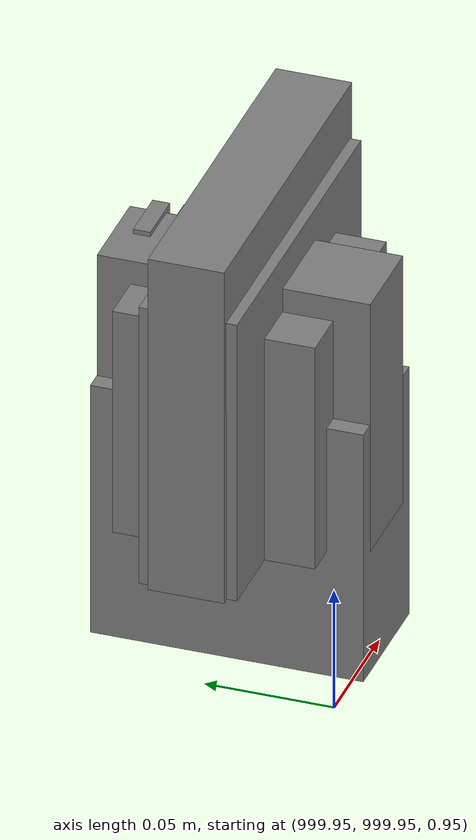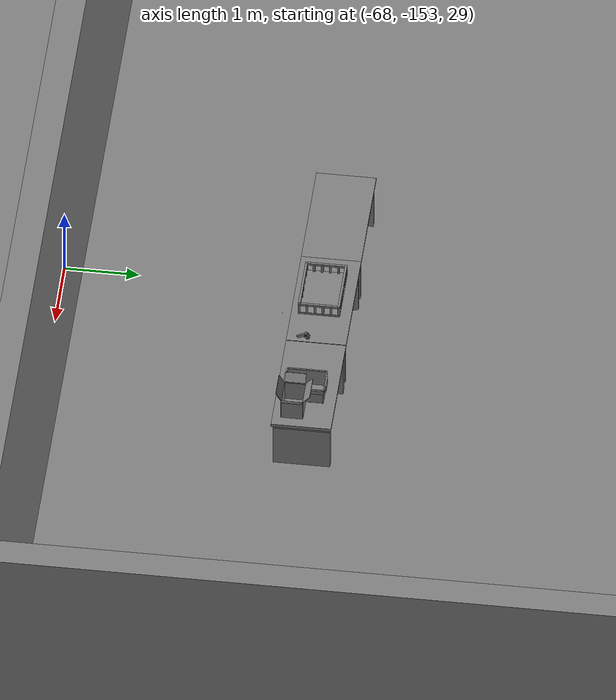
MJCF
<mujoco>
    <option gravity="0.000000000 0.000000000 -9.810000420" timestep="0.0049999999" integrator="implicitfast" density="1.225" viscosity="1.8000001e-05" noslip_iterations="10" iterations="100" sdf_iterations="50">
        <flag multiccd="disable"/>
    </option>
    <size memory="1000M"/>
    <compiler coordinate="local"/>
    <worldbody>
        <light cutoff="30" pos="0 1 1" dir="0 -1 -2"/>
        <light cutoff="30" pos="0 -1 1" dir="0 1 -2"/>
        <body pos="-66.311050415 -149.359573364 31.162393570" euler="-38.940750122 64.150032043 -39.546047211" mocap="true" name="spotlight4_SpotLight"/>
        <body pos="-66.279380798 -148.976867676 31.167718887" euler="-100.004531860 70.545219421 -25.885787964" mocap="true" name="spotlight2_SpotLight"/>
        <body pos="1000.000000000 1000.000000000 1.000000000" euler="0.000000000 0.000000000 180.000000000" name="openloong_gripper_2f85_fix_base_usda_battery_01">
            <geom contype="1" conaffinity="1" density="1000" type="box" material="" rgba="0.500000000 0.500000000 0.500000000 1.000000000" solimp="0.899999976 0.949999988 0.001000000" friction="1.000000000 0.005000000 0.000100000" solref="0.020000000 1.000000000" margin="0" condim="3" group="0" pos="-0.011123657 -0.041940309 0.101691343" quat="1.000000000 0.000000000 0.000000000 0.000000000" size="0.010800000 0.003375000 0.004725000" name="openloong_gripper_2f85_fix_base_usda_geom_CA97930E_8034_453A_BA41_BCFD67BC07E8"/>
            <geom contype="1" conaffinity="1" density="1000" type="box" material="" rgba="0.500000000 0.500000000 0.500000000 1.000000000" solimp="0.899999976 0.949999988 0.001000000" friction="1.000000000 0.005000000 0.000100000" solref="0.020000000 1.000000000" margin="0" condim="3" group="0" pos="-0.010876465 -0.044247437 0.047066893" quat="0.998702705 -0.050920475 0.000000000 0.000000000" size="0.009450001 0.002700000 0.024975000" name="openloong_gripper_2f85_fix_base_usda_geom_B76E9502_15B9_44E7_B6A4_6B4F3CF13453"/>
            <geom contype="1" conaffinity="1" density="1000" type="box" material="" rgba="0.500000000 0.500000000 0.500000000 1.000000000" solimp="0.899999976 0.949999988 0.001000000" friction="1.000000000 0.005000000 0.000100000" solref="0.020000000 1.000000000" margin="0" condim="3" group="0" pos="-0.001235962 -0.000659180 0.047381196" quat="1.000000000 0.000000000 0.000000000 0.000000000" size="0.039420001 0.039150000 0.047250003" name="openloong_gripper_2f85_fix_base_usda_geom_C212A112_29AB_4ED8_B23D_E6D379A3257E"/>
            <geom contype="1" conaffinity="1" density="1000" type="box" material="" rgba="0.500000000 0.500000000 0.500000000 1.000000000" solimp="0.899999976 0.949999988 0.001000000" friction="1.000000000 0.005000000 0.000100000" solref="0.020000000 1.000000000" margin="0" condim="3" group="0" pos="-0.010876465 -0.039138794 0.009851727" quat="1.000000000 0.000000000 0.000000000 0.000000000" size="0.009450001 0.010800000 0.013500000" name="openloong_gripper_2f85_fix_base_usda_geom_3460FF2F_EB54_438A_996A_F3673F8E1E9A"/>
            <geom contype="1" conaffinity="1" density="1000" type="box" material="" rgba="0.500000000 0.500000000 0.500000000 1.000000000" solimp="0.899999976 0.949999988 0.001000000" friction="1.000000000 0.005000000 0.000100000" solref="0.020000000 1.000000000" margin="0" condim="3" group="0" pos="-0.010876465 -0.041528322 0.071508206" quat="1.000000000 0.000000000 0.000000000 0.000000000" size="0.009450001 0.002700000 0.027000001" name="openloong_gripper_2f85_fix_base_usda_geom_79A7131E_C967_4A51_8E63_008E0326CBE6"/>
            <freejoint name="openloong_gripper_2f85_fix_base_usda_battery_01_joint"/>
            <site size="0.005000000 0.005000000 0.005000000" rgba="0.500000000 0.500000000 0.500000000 1.000000000" pos="0.000000000 0.000000000 0.000000000" quat="0.999961913 0.008726500 0.000000000 0.000000000" group="0" type="sphere" name="openloong_gripper_2f85_fix_base_usda_battery_01site"/>
        </body>
        <body pos="1000.000000000 1000.000000000 1.000000000" euler="0.000000000 0.000000000 180.000000000" name="openloong_gripper_2f85_fix_base_usda_cpu_fan">
            <geom contype="1" conaffinity="1" density="1000" type="box" material="" rgba="0.500000000 0.500000000 0.500000000 1.000000000" solimp="0.899999976 0.949999988 0.001000000" friction="1.000000000 0.005000000 0.000100000" solref="0.020000000 1.000000000" margin="0" condim="3" group="0" pos="0.000000000 0.000000000 0.070034981" quat="0.000000000 0.000000000 0.000000000 1.000000000" size="0.070700005 0.014699999 0.070700005" name="openloong_gripper_2f85_fix_base_usda_geom_FFF3C70B_BDB7_43ED_ABB1_0C373AA654E6"/>
            <freejoint name="openloong_gripper_2f85_fix_base_usda_cpu_fan_joint"/>
            <site size="0.005000000 0.005000000 0.005000000" rgba="0.500000000 0.500000000 0.500000000 1.000000000" pos="0.000000000 0.000000000 0.000000000" quat="0.999961913 0.008726535 0.000000000 0.000000000" group="0" type="sphere" name="openloong_gripper_2f85_fix_base_usda_cpu_fancsite"/>
        </body>
        <body pos="1000.000000000 1000.000000000 1.000000000" euler="0.000000000 0.000000000 180.000000000" name="openloong_gripper_2f85_fix_base_usda_wifi_box">
            <geom contype="1" conaffinity="1" density="1000" type="box" material="" rgba="0.500000000 0.500000000 0.500000000 1.000000000" solimp="0.899999976 0.949999988 0.001000000" friction="1.000000000 0.005000000 0.000100000" solref="0.020000000 1.000000000" margin="0" condim="3" group="0" pos="0.000000000 0.000000000 0.058978677" quat="0.000000000 0.000000047 0.000000000 1.000000000" size="0.068499997 0.018999999 0.059000000" name="openloong_gripper_2f85_fix_base_usda_geom_FB7C8F67_6D49_4435_9C62_A68A21D657D3"/>
            <freejoint name="openloong_gripper_2f85_fix_base_usda_wifi_box_joint"/>
            <site size="0.005000000 0.005000000 0.005000000" rgba="0.500000000 0.500000000 0.500000000 1.000000000" pos="0.000000000 0.000000000 0.000000000" quat="0.999961913 0.008726500 0.000000000 0.000000000" group="0" type="sphere" name="openloong_gripper_2f85_fix_base_usda_wifi_boxsite"/>
        </body>
        <body pos="1000.000000000 1000.000000000 1.000000000" euler="0.000011953 0.000005123 -179.999984741" name="openloong_gripper_2f85_fix_base_usda_intel_box">
            <geom contype="1" conaffinity="1" density="1000" type="box" material="" rgba="0.500000000 0.500000000 0.500000000 1.000000000" solimp="0.899999976 0.949999988 0.001000000" friction="1.000000000 0.005000000 0.000100000" solref="0.020000000 1.000000000" margin="0" condim="3" group="0" pos="0.000000000 -0.000067139 0.000082284" quat="0.707106709 0.000000225 0.000000253 0.707106650" size="0.052800003 0.025300000 0.052800003" name="openloong_gripper_2f85_fix_base_usda_geom_DB365E63_2636_48B7_AD14_A8B2C1B34630"/>
            <freejoint name="openloong_gripper_2f85_fix_base_usda_intel_box_joint"/>
            <site size="0.005000000 0.005000000 0.005000000" rgba="0.500000000 0.500000000 0.500000000 1.000000000" pos="0.000000000 0.000000000 0.000000000" quat="0.999961913 0.008726500 0.000000000 0.000000000" group="0" type="sphere" name="openloong_gripper_2f85_fix_base_usda_intel_boxsite"/>
        </body>
        <body pos="-66.369285583 -149.476669312 31.171352386" euler="-3.945538759 13.528707504 -88.510185242" mocap="true" name="spotlight5_SpotLight"/>
        <body pos="1000.000000000 999.999938965 1.000000000" euler="0.000000000 0.000000000 180.000000000" name="openloong_gripper_2f85_fix_base_usda_intelcore_i5">
            <geom contype="1" conaffinity="1" density="1000" type="box" material="" rgba="0.500000000 0.500000000 0.500000000 1.000000000" solimp="0.899999976 0.949999988 0.001000000" friction="1.000000000 0.005000000 0.000100000" solref="0.020000000 1.000000000" margin="0" condim="3" group="0" pos="0.000000000 0.000000000 0.051722717" quat="0.707106709 0.000000000 0.000000000 -0.707106769" size="0.052800000 0.018080002 0.052800000" name="openloong_gripper_2f85_fix_base_usda_geom_8CD62439_095D_4E0C_866D_CC22031CA970"/>
            <freejoint name="openloong_gripper_2f85_fix_base_usda_intelcore_i5_joint"/>
            <site size="0.005000000 0.005000000 0.005000000" rgba="0.500000000 0.500000000 0.500000000 1.000000000" pos="0.000000000 0.000000000 0.000000000" quat="0.999961913 0.008726534 0.000000000 0.000000000" group="0" type="sphere" name="openloong_gripper_2f85_fix_base_usda_intelcore_i5site"/>
        </body>
        <body pos="-64.866622925 -149.383972168 30.183746338" euler="89.999984741 89.999946594 0.000000000" name="openloong_gripper_2f85_fix_base_usda_bluebox_01">
            <geom contype="1" conaffinity="1" density="1000" type="box" material="" rgba="0.500000000 0.500000000 0.500000000 1.000000000" solimp="0.899999976 0.949999988 0.001000000" friction="1.000000000 0.005000000 0.000100000" solref="0.020000000 1.000000000" margin="0" condim="3" group="0" pos="0.276580811 0.187225342 0.000068665" quat="0.707106948 0.000077471 0.707106352 0.000077486" size="0.100000001 0.057999998 0.010000000" name="openloong_gripper_2f85_fix_base_usda_geom_31130C46_16B1_4FB8_BB3C_77FA81DA9972"/>
            <geom contype="1" conaffinity="1" density="1000" type="box" material="" rgba="0.500000000 0.500000000 0.500000000 1.000000000" solimp="0.899999976 0.949999988 0.001000000" friction="1.000000000 0.005000000 0.000100000" solref="0.020000000 1.000000000" margin="0" condim="3" group="0" pos="0.000000000 0.002883911 0.000000000" quat="0.999999881 0.000000000 0.000000000 0.000000000" size="0.254000008 0.003000000 0.172000006" name="openloong_gripper_2f85_fix_base_usda_geom_573A94FB_205E_4B65_A0DF_CC7F0FAAA956"/>
            <geom contype="1" conaffinity="1" density="1000" type="box" material="" rgba="0.500000000 0.500000000 0.500000000 1.000000000" solimp="0.899999976 0.949999988 0.001000000" friction="1.000000000 0.005000000 0.000100000" solref="0.020000000 1.000000000" margin="0" condim="3" group="0" pos="0.000000000 0.124874115 0.173484802" quat="0.999796331 0.020176515 -0.000000015 0.000000030" size="0.259999990 0.119999997 0.007000000" name="openloong_gripper_2f85_fix_base_usda_geom_B37E208F_AFD6_43C9_98CB_75885FEE57A5"/>
            <geom contype="1" conaffinity="1" density="1000" type="box" material="" rgba="0.500000000 0.500000000 0.500000000 1.000000000" solimp="0.899999976 0.949999988 0.001000000" friction="1.000000000 0.005000000 0.000100000" solref="0.020000000 1.000000000" margin="0" condim="3" group="0" pos="0.000000000 0.124874115 -0.173469543" quat="0.999796331 -0.020176545 -0.000000015 0.000000000" size="0.259999990 0.119999997 0.007000000" name="openloong_gripper_2f85_fix_base_usda_geom_13E7B3AF_D7C1_46E7_95A1_028357115F12"/>
            <geom contype="1" conaffinity="1" density="1000" type="box" material="" rgba="0.500000000 0.500000000 0.500000000 1.000000000" solimp="0.899999976 0.949999988 0.001000000" friction="1.000000000 0.005000000 0.000100000" solref="0.020000000 1.000000000" margin="0" condim="3" group="0" pos="0.000000000 0.214008331 0.188980103" quat="0.999912977 0.013176724 0.000000015 0.000000000" size="0.259999990 0.029999999 0.012500000" name="openloong_gripper_2f85_fix_base_usda_geom_3333BA6D_3BF1_40E9_AE0D_83DC03D8BF43"/>
            <geom contype="1" conaffinity="1" density="1000" type="box" material="" rgba="0.500000000 0.500000000 0.500000000 1.000000000" solimp="0.899999976 0.949999988 0.001000000" friction="1.000000000 0.005000000 0.000100000" solref="0.020000000 1.000000000" margin="0" condim="3" group="0" pos="-0.258361816 0.125289917 0.001876831" quat="0.702796936 -0.020792112 0.710783124 0.020769298" size="0.189999998 0.119999997 0.009000000" name="openloong_gripper_2f85_fix_base_usda_geom_F07E78CE_80BC_4080_A79B_78305504CE60"/>
            <geom contype="1" conaffinity="1" density="1000" type="box" material="" rgba="0.500000000 0.500000000 0.500000000 1.000000000" solimp="0.899999976 0.949999988 0.001000000" friction="1.000000000 0.005000000 0.000100000" solref="0.020000000 1.000000000" margin="0" condim="3" group="0" pos="0.000000000 0.214008331 -0.188980103" quat="0.999912977 -0.013176769 0.000000030 0.000000015" size="0.259999990 0.029999999 0.012500000" name="openloong_gripper_2f85_fix_base_usda_geom_E2D8B79A_9547_4FE4_9DCD_68F484A9F18E"/>
            <geom contype="1" conaffinity="1" density="1000" type="box" material="" rgba="0.500000000 0.500000000 0.500000000 1.000000000" solimp="0.899999976 0.949999988 0.001000000" friction="1.000000000 0.005000000 0.000100000" solref="0.020000000 1.000000000" margin="0" condim="3" group="0" pos="-0.276611328 0.187225342 0.000068665" quat="0.707106650 0.000077441 0.707106709 0.000077456" size="0.100000001 0.057999998 0.010000000" name="openloong_gripper_2f85_fix_base_usda_geom_1D2954C6_D436_4CDA_A135_D22C0DC271D4"/>
            <geom contype="1" conaffinity="1" density="1000" type="box" material="" rgba="0.500000000 0.500000000 0.500000000 1.000000000" solimp="0.899999976 0.949999988 0.001000000" friction="1.000000000 0.005000000 0.000100000" solref="0.020000000 1.000000000" margin="0" condim="3" group="0" pos="0.258331299 0.125289917 0.001876831" quat="0.702851415 0.018856421 0.710823774 -0.019329369" size="0.189999998 0.119999997 0.009000000" name="openloong_gripper_2f85_fix_base_usda_geom_A63EFFCC_6DEE_497F_A74B_F2E8E5D5E56D"/>
            <freejoint name="openloong_gripper_2f85_fix_base_usda_bluebox_01_joint"/>
            <site size="0.005000000 0.005000000 0.005000000" rgba="0.500000000 0.500000000 0.500000000 1.000000000" pos="0.000000000 0.000000000 0.000000000" quat="0.999961913 0.008726534 0.000000000 0.000000000" group="0" type="sphere" name="openloong_gripper_2f85_fix_base_usda_bluebox_01site"/>
        </body>
        <body pos="-64.496299744 -149.491867065 30.235729218" euler="0.000000000 0.000000000 89.999946594" name="openloong_gripper_2f85_fix_base_usda_cardboardbox_01">
            <geom contype="1" conaffinity="1" density="1000" type="box" material="" rgba="0.500000000 0.500000000 0.500000000 1.000000000" solimp="0.899999976 0.949999988 0.001000000" friction="1.000000000 0.005000000 0.000100000" solref="0.020000000 1.000000000" margin="0" condim="3" group="0" pos="-0.003166199 -0.004086494 0.005052090" quat="1.000000000 0.000000000 0.000000000 0.000000000" size="0.142499998 0.177500010 0.005000000" name="openloong_gripper_2f85_fix_base_usda_geom_A689D8E0_B514_4BD8_9339_7CDF0D7DAE81"/>
            <geom contype="1" conaffinity="1" density="1000" type="box" material="" rgba="0.500000000 0.500000000 0.500000000 1.000000000" solimp="0.899999976 0.949999988 0.001000000" friction="1.000000000 0.005000000 0.000100000" solref="0.020000000 1.000000000" margin="0" condim="3" group="0" pos="-0.003166199 0.170316696 0.150570869" quat="1.000000000 0.000000000 0.000000000 0.000000000" size="0.142499998 0.005000000 0.149999991" name="openloong_gripper_2f85_fix_base_usda_geom_42A3D74B_4DD9_4405_909A_1FC897F29DDC"/>
            <geom contype="1" conaffinity="1" density="1000" type="box" material="" rgba="0.500000000 0.500000000 0.500000000 1.000000000" solimp="0.899999976 0.949999988 0.001000000" friction="1.000000000 0.005000000 0.000100000" solref="0.020000000 1.000000000" margin="0" condim="3" group="0" pos="-0.147399902 -0.005307198 0.150570869" quat="1.000000000 0.000000000 0.000000000 0.000000000" size="0.005000000 0.177500010 0.149999991" name="openloong_gripper_2f85_fix_base_usda_geom_DA5CD34A_35DF_4092_B20A_0261F4DC6993"/>
            <geom contype="1" conaffinity="1" density="1000" type="box" material="" rgba="0.500000000 0.500000000 0.500000000 1.000000000" solimp="0.899999976 0.949999988 0.001000000" friction="1.000000000 0.005000000 0.000100000" solref="0.020000000 1.000000000" margin="0" condim="3" group="0" pos="0.140275955 -0.005307198 0.150570869" quat="1.000000000 0.000000000 0.000000000 0.000000000" size="0.005000000 0.177500010 0.149999991" name="openloong_gripper_2f85_fix_base_usda_geom_174901BF_4760_48FF_BCA6_559FA509084B"/>
            <geom contype="1" conaffinity="1" density="1000" type="box" material="" rgba="0.500000000 0.500000000 0.500000000 1.000000000" solimp="0.899999976 0.949999988 0.001000000" friction="1.000000000 0.005000000 0.000100000" solref="0.020000000 1.000000000" margin="0" condim="3" group="0" pos="-0.003166199 -0.181550980 0.150570869" quat="1.000000000 0.000000000 0.000000000 0.000000000" size="0.142499998 0.005000000 0.149999991" name="openloong_gripper_2f85_fix_base_usda_geom_E7CA4337_7E19_47E8_91E2_2393E13EA417"/>
            <freejoint name="openloong_gripper_2f85_fix_base_usda_cardboardbox_01_joint"/>
            <site size="0.005000000 0.005000000 0.005000000" rgba="0.500000000 0.500000000 0.500000000 1.000000000" pos="0.000000000 0.000000000 0.000000000" quat="0.999961913 0.008726535 0.000000000 0.000000000" group="0" type="sphere" name="openloong_gripper_2f85_fix_base_usda_site_06B14B1E_546F_4F68_91C8_69B53CFD9EDB"/>
            <body pos="0.139160156 -0.004048347 0.301930904" euler="-179.999954224 49.383502960 179.999954224" name="openloong_gripper_2f85_fix_base_usda_A1_006">
                <geom contype="1" conaffinity="1" density="1000" type="box" material="" rgba="0.500000000 0.500000000 0.500000000 1.000000000" solimp="0.899999976 0.949999988 0.001000000" friction="1.000000000 0.005000000 0.000100000" solref="0.020000000 1.000000000" margin="0" condim="3" group="0" pos="-0.071587563 0.000009537 0.001745224" quat="0.999999881 0.000000000 0.000000000 0.000000000" size="0.071249999 0.179999992 0.002500000" name="openloong_gripper_2f85_fix_base_usda_geom_6E8EB685_DC30_4CA1_8445_BBE5850FF096"/>
                <joint armature="0" stiffness="0.07" damping="0.0099999998" axis="0.000000 1.000000 0.000000" type="hinge" name="openloong_gripper_2f85_fix_base_usda_A1_006"/>
            </body>
            <body pos="-0.145902634 -0.004086494 0.301938057" euler="-180.000000000 -60.000011444 -180.000000000" name="openloong_gripper_2f85_fix_base_usda_A2_006">
                <geom contype="1" conaffinity="1" density="1000" type="box" material="" rgba="0.500000000 0.500000000 0.500000000 1.000000000" solimp="0.899999976 0.949999988 0.001000000" friction="1.000000000 0.005000000 0.000100000" solref="0.020000000 1.000000000" margin="0" condim="3" group="0" pos="0.071268082 0.000009537 0.002717972" quat="0.000002921 0.000000000 -0.000000030 0.999999881" size="0.071249999 0.179999992 0.002500000" name="openloong_gripper_2f85_fix_base_usda_geom_118EB721_B580_45C1_8232_18A29F87B3F0"/>
                <joint armature="0" stiffness="0.07" damping="0.0099999998" axis="0.000000 1.000000 0.000000" type="hinge" name="openloong_gripper_2f85_fix_base_usda_A2_006"/>
            </body>
            <body pos="-0.003385544 0.175991058 0.301930904" euler="-125.858116150 -0.000004561 0.000002331" name="openloong_gripper_2f85_fix_base_usda_B2_006">
                <geom contype="1" conaffinity="1" density="1000" type="box" material="" rgba="0.500000000 0.500000000 0.500000000 1.000000000" solimp="0.899999976 0.949999988 0.001000000" friction="1.000000000 0.005000000 0.000100000" solref="0.020000000 1.000000000" margin="0" condim="3" group="0" pos="0.000009537 -0.070939064 -0.002470016" quat="0.999614120 0.027776197 -0.000000015 0.000000030" size="0.137500003 0.064999998 0.005000000" name="openloong_gripper_2f85_fix_base_usda_geom_C428F805_C6BE_42F0_96F1_687542D6901E"/>
                <joint armature="0" stiffness="0.07" damping="0.0099999998" axis="1.000000 0.000000 0.000000" type="hinge" name="openloong_gripper_2f85_fix_base_usda_B2_006"/>
            </body>
            <body pos="-0.003385544 -0.184140205 0.301938057" euler="147.805557251 0.000000000 0.000000000" name="openloong_gripper_2f85_fix_base_usda_B1_006">
                <geom contype="1" conaffinity="1" density="1000" type="box" material="" rgba="0.500000000 0.500000000 0.500000000 1.000000000" solimp="0.899999976 0.949999988 0.001000000" friction="1.000000000 0.005000000 0.000100000" solref="0.020000000 1.000000000" margin="0" condim="3" group="0" pos="-0.000028610 0.070202351 -0.002703667" quat="0.999614179 -0.027776167 0.000000000 0.000000000" size="0.137500003 0.064999998 0.005000000" name="openloong_gripper_2f85_fix_base_usda_geom_7B8FA03B_536F_4374_B868_15F5375085BF"/>
                <joint armature="0" stiffness="0.07" damping="0.0099999998" axis="1.000000 0.000000 0.000000" type="hinge" name="openloong_gripper_2f85_fix_base_usda_B1_006"/>
            </body>
        </body>
        <body pos="-65.882858276 -149.481979370 30.229999542" euler="-64.487716675 0.000000000 0.000000000" name="openloong_gripper_2f85_fix_base_usda_Barcode">
            <geom contype="1" conaffinity="1" density="1000" type="box" material="" rgba="0.500000000 0.500000000 0.500000000 1.000000000" solimp="0.899999976 0.949999988 0.001000000" friction="1.000000000 0.005000000 0.000100000" solref="0.020000000 1.000000000" margin="0" condim="3" group="0" pos="0.000000000 0.013038635 0.001419067" quat="0.000000000 0.000000000 0.000000000 1.000000119" size="0.034000002 0.010000000 0.017999999" name="openloong_gripper_2f85_fix_base_usda_geom_95069102_573B_4658_BE5F_B15978162C5D"/>
            <geom contype="1" conaffinity="1" density="1000" type="box" material="" rgba="0.500000000 0.500000000 0.500000000 1.000000000" solimp="0.899999976 0.949999988 0.001000000" friction="1.000000000 0.005000000 0.000100000" solref="0.020000000 1.000000000" margin="0" condim="3" group="0" pos="0.000000000 -0.035301208 -0.007095337" quat="0.000000000 0.000000000 -0.043619365 0.999048233" size="0.028999999 0.010000000 0.020000000" name="openloong_gripper_2f85_fix_base_usda_geom_78F30FCD_7FE4_470F_A182_1A74E087BC2C"/>
            <geom contype="1" conaffinity="1" density="1000" type="box" material="" rgba="0.500000000 0.500000000 0.500000000 1.000000000" solimp="0.899999976 0.949999988 0.001000000" friction="1.000000000 0.005000000 0.000100000" solref="0.020000000 1.000000000" margin="0" condim="3" group="0" pos="0.000000000 -0.043411255 -0.011749268" quat="0.922262907 0.386563420 0.000000000 0.000000000" size="0.026000001 0.010000000 0.020000000" name="openloong_gripper_2f85_fix_base_usda_geom_34D355AC_B0DA_4BDB_A8CC_578C8569793B"/>
            <geom contype="1" conaffinity="1" density="1000" type="box" material="" rgba="0.500000000 0.500000000 0.500000000 1.000000000" solimp="0.899999976 0.949999988 0.001000000" friction="1.000000000 0.005000000 0.000100000" solref="0.020000000 1.000000000" margin="0" condim="3" group="0" pos="0.000000000 -0.016967773 -0.031860352" quat="0.000000000 0.000000000 0.000000000 1.000000119" size="0.008000000 0.010000000 0.013000000" name="openloong_gripper_2f85_fix_base_usda_geom_2AD4D0A7_BD24_4D9C_8FB7_3188DDFE23BF"/>
            <geom contype="1" conaffinity="1" density="1000" type="box" material="" rgba="0.500000000 0.500000000 0.500000000 1.000000000" solimp="0.899999976 0.949999988 0.001000000" friction="1.000000000 0.005000000 0.000100000" solref="0.020000000 1.000000000" margin="0" condim="3" group="0" pos="0.000000000 -0.001869202 0.000312805" quat="0.953716993 0.300705761 0.000000000 0.000000000" size="0.032000002 0.010000000 0.018999999" name="openloong_gripper_2f85_fix_base_usda_geom_ACA5D6F7_BB19_4C94_BC19_7F502033F495"/>
            <geom contype="1" conaffinity="1" density="1000" type="box" material="" rgba="0.500000000 0.500000000 0.500000000 1.000000000" solimp="0.899999976 0.949999988 0.001000000" friction="1.000000000 0.005000000 0.000100000" solref="0.020000000 1.000000000" margin="0" condim="3" group="0" pos="0.000000000 -0.019531250 -0.003173828" quat="0.953716993 0.300705761 0.000000000 0.000000000" size="0.030999999 0.010000000 0.020000000" name="openloong_gripper_2f85_fix_base_usda_geom_1C8F6428_B5AE_4C07_846F_A96B289FD264"/>
            <geom contype="1" conaffinity="1" density="1000" type="box" material="" rgba="0.500000000 0.500000000 0.500000000 1.000000000" solimp="0.899999976 0.949999988 0.001000000" friction="1.000000000 0.005000000 0.000100000" solref="0.020000000 1.000000000" margin="0" condim="3" group="0" pos="0.000000000 -0.035301208 -0.007095337" quat="0.953716993 0.300705761 0.000000000 0.000000000" size="0.028999999 0.010000000 0.020000000" name="openloong_gripper_2f85_fix_base_usda_geom_D54427F2_0B02_4720_B17E_EC1D0F07A979"/>
            <geom contype="1" conaffinity="1" density="1000" type="box" material="" rgba="0.500000000 0.500000000 0.500000000 1.000000000" solimp="0.899999976 0.949999988 0.001000000" friction="1.000000000 0.005000000 0.000100000" solref="0.020000000 1.000000000" margin="0" condim="3" group="0" pos="0.000000000 -0.042617798 -0.071121216" quat="0.000000000 0.000000000 0.000000000 1.000000119" size="0.013000000 0.021000000 0.059999999" name="openloong_gripper_2f85_fix_base_usda_geom_3F77D7CB_D006_4967_9F20_4A326FFCCDDC"/>
            <freejoint name="openloong_gripper_2f85_fix_base_usda_Barcode_joint"/>
            <site size="0.005000000 0.005000000 0.005000000" rgba="0.500000000 0.500000000 0.500000000 1.000000000" pos="0.000000000 0.000000000 0.000000000" quat="1.000000000 0.000000000 0.000000000 0.000000000" group="0" type="sphere" name="openloong_gripper_2f85_fix_base_usda_Barcode_site"/>
        </body>
        <body pos="-66.745018005 -149.392349243 30.184000015" euler="0.000000000 0.000000000 89.999946594" name="[22332422694131]_Basket_01">
            <geom contype="1" conaffinity="1" density="1000" type="box" material="" rgba="0.500000000 0.500000000 0.500000000 1.000000000" solimp="0.899999976 0.949999988 0.001000000" friction="1.000000000 0.005000000 0.000100000" solref="0.020000000 1.000000000" margin="0" condim="3" group="0" pos="-0.052425385 0.389207840 0.089787483" quat="0.707107008 0.000000000 0.000000000 0.707106411" size="0.014249999 0.014249999 0.059999999" name="[22332422694131]_geom_E8EBE19B_E7FD_43F4_99E8_93FEB9C54B41"/>
            <geom contype="1" conaffinity="1" density="1000" type="box" material="" rgba="0.500000000 0.500000000 0.500000000 1.000000000" solimp="0.899999976 0.949999988 0.001000000" friction="1.000000000 0.005000000 0.000100000" solref="0.020000000 1.000000000" margin="0" condim="3" group="0" pos="0.264015198 -0.133043289 0.089787483" quat="0.707107008 0.000000000 0.000000000 0.707106411" size="0.014249999 0.014249999 0.059999999" name="[22332422694131]_geom_89FAE18B_7F30_45E5_BAF9_E22FA526D6F1"/>
            <geom contype="1" conaffinity="1" density="1000" type="box" material="" rgba="0.500000000 0.500000000 0.500000000 1.000000000" solimp="0.899999976 0.949999988 0.001000000" friction="1.000000000 0.005000000 0.000100000" solref="0.020000000 1.000000000" margin="0" condim="3" group="0" pos="-0.264015198 -0.265548706 0.089793205" quat="0.707107008 0.000000000 0.000000000 0.707106411" size="0.014249999 0.014249999 0.059999999" name="[22332422694131]_geom_2208DC0C_A25F_4783_9ED7_A0CE5E16EDF3"/>
            <geom contype="1" conaffinity="1" density="1000" type="box" material="" rgba="0.500000000 0.500000000 0.500000000 1.000000000" solimp="0.899999976 0.949999988 0.001000000" friction="1.000000000 0.005000000 0.000100000" solref="0.020000000 1.000000000" margin="0" condim="3" group="0" pos="-0.160263062 -0.389322281 0.089793205" quat="0.707107008 0.000000000 0.000000000 0.707106411" size="0.014249999 0.014249999 0.059999999" name="[22332422694131]_geom_5B8A61D8_8F92_4855_8845_915FA0CF1C8A"/>
            <geom contype="1" conaffinity="1" density="1000" type="box" material="" rgba="0.500000000 0.500000000 0.500000000 1.000000000" solimp="0.899999976 0.949999988 0.001000000" friction="1.000000000 0.005000000 0.000100000" solref="0.020000000 1.000000000" margin="0" condim="3" group="0" pos="0.162265778 -0.389322281 0.089787483" quat="0.707107008 0.000000000 0.000000000 0.707106411" size="0.014249999 0.014249999 0.059999999" name="[22332422694131]_geom_0C74A162_5D10_4283_A180_CED97CA6F108"/>
            <geom contype="1" conaffinity="1" density="1000" type="box" material="" rgba="0.500000000 0.500000000 0.500000000 1.000000000" solimp="0.899999976 0.949999988 0.001000000" friction="1.000000000 0.005000000 0.000100000" solref="0.020000000 1.000000000" margin="0" condim="3" group="0" pos="0.264015198 0.389207840 0.089787483" quat="0.707107008 0.000000000 0.000000000 0.707106411" size="0.014249999 0.014249999 0.059999999" name="[22332422694131]_geom_2604307C_0E83_4254_B0DE_8D5518005B7A"/>
            <geom contype="1" conaffinity="1" density="1000" type="box" material="" rgba="0.500000000 0.500000000 0.500000000 1.000000000" solimp="0.899999976 0.949999988 0.001000000" friction="1.000000000 0.005000000 0.000100000" solref="0.020000000 1.000000000" margin="0" condim="3" group="0" pos="-0.264015198 -0.133043289 0.089793205" quat="0.707107008 0.000000000 0.000000000 0.707106411" size="0.014249999 0.014249999 0.059999999" name="[22332422694131]_geom_7AA1AE30_1674_4D36_BB87_A1E80FCC706B"/>
            <geom contype="1" conaffinity="1" density="1000" type="box" material="" rgba="0.500000000 0.500000000 0.500000000 1.000000000" solimp="0.899999976 0.949999988 0.001000000" friction="1.000000000 0.005000000 0.000100000" solref="0.020000000 1.000000000" margin="0" condim="3" group="0" pos="-0.264026642 0.269256592 0.089793205" quat="0.707107008 0.000000000 0.000000000 0.707106411" size="0.014249999 0.014249999 0.059999999" name="[22332422694131]_geom_D5C82F1B_D7F7_4FAF_84BC_928AF59D3549"/>
            <geom contype="1" conaffinity="1" density="1000" type="box" material="" rgba="0.500000000 0.500000000 0.500000000 1.000000000" solimp="0.899999976 0.949999988 0.001000000" friction="1.000000000 0.005000000 0.000100000" solref="0.020000000 1.000000000" margin="0" condim="3" group="0" pos="0.054462433 0.389207840 0.089787483" quat="0.707107008 0.000000000 0.000000000 0.707106411" size="0.014249999 0.014249999 0.059999999" name="[22332422694131]_geom_EF4F2EE1_F651_455E_9B14_09616322FA44"/>
            <geom contype="1" conaffinity="1" density="1000" type="box" material="" rgba="0.500000000 0.500000000 0.500000000 1.000000000" solimp="0.899999976 0.949999988 0.001000000" friction="1.000000000 0.005000000 0.000100000" solref="0.020000000 1.000000000" margin="0" condim="3" group="0" pos="0.054462433 -0.389322281 0.089787483" quat="0.707107008 0.000000000 0.000000000 0.707106411" size="0.014249999 0.014249999 0.059999999" name="[22332422694131]_geom_42EA3DEA_3794_496E_A38A_287A008F7535"/>
            <geom contype="1" conaffinity="1" density="1000" type="box" material="" rgba="0.500000000 0.500000000 0.500000000 1.000000000" solimp="0.899999976 0.949999988 0.001000000" friction="1.000000000 0.005000000 0.000100000" solref="0.020000000 1.000000000" margin="0" condim="3" group="0" pos="0.264015198 0.269256592 0.089793205" quat="0.707107008 0.000000000 0.000000000 0.707106411" size="0.014249999 0.014249999 0.059999999" name="[22332422694131]_geom_5BB0F636_1248_422E_A402_3A64A91A97D4"/>
            <geom contype="1" conaffinity="1" density="1000" type="box" material="" rgba="0.500000000 0.500000000 0.500000000 1.000000000" solimp="0.899999976 0.949999988 0.001000000" friction="1.000000000 0.005000000 0.000100000" solref="0.020000000 1.000000000" margin="0" condim="3" group="0" pos="0.264015198 -0.389322281 0.089787483" quat="0.707107008 0.000000000 0.000000000 0.707106411" size="0.014249999 0.014249999 0.059999999" name="[22332422694131]_geom_803AE79B_2779_4760_B3C3_74389498AA51"/>
            <geom contype="1" conaffinity="1" density="1000" type="box" material="" rgba="0.500000000 0.500000000 0.500000000 1.000000000" solimp="0.899999976 0.949999988 0.001000000" friction="1.000000000 0.005000000 0.000100000" solref="0.020000000 1.000000000" margin="0" condim="3" group="0" pos="0.000000000 0.000000000 0.015998840" quat="0.707107008 0.000000000 0.000000000 0.707106411" size="0.403499991 0.279000014 0.015750000" name="[22332422694131]_geom_2B3A54A2_78FF_4FAB_B771_A65DD0739ECB"/>
            <geom contype="1" conaffinity="1" density="1000" type="box" material="" rgba="0.500000000 0.500000000 0.500000000 1.000000000" solimp="0.899999976 0.949999988 0.001000000" friction="1.000000000 0.005000000 0.000100000" solref="0.020000000 1.000000000" margin="0" condim="3" group="0" pos="0.000000000 -0.389476776 0.163619041" quat="0.707107008 0.000000000 0.000000000 0.707106411" size="0.015000000 0.277500004 0.015750000" name="[22332422694131]_geom_BF9CFF24_C90F_430D_8E6D_044BC5327F5F"/>
            <geom contype="1" conaffinity="1" density="1000" type="box" material="" rgba="0.500000000 0.500000000 0.500000000 1.000000000" solimp="0.899999976 0.949999988 0.001000000" friction="1.000000000 0.005000000 0.000100000" solref="0.020000000 1.000000000" margin="0" condim="3" group="0" pos="0.162265778 0.389207840 0.089787483" quat="0.707107008 0.000000000 0.000000000 0.707106411" size="0.014249999 0.014249999 0.059999999" name="[22332422694131]_geom_2F1C9BC8_5F4D_4558_9489_C193ED64532E"/>
            <geom contype="1" conaffinity="1" density="1000" type="box" material="" rgba="0.500000000 0.500000000 0.500000000 1.000000000" solimp="0.899999976 0.949999988 0.001000000" friction="1.000000000 0.005000000 0.000100000" solref="0.020000000 1.000000000" margin="0" condim="3" group="0" pos="0.000000000 0.389471054 0.163619041" quat="0.707107008 0.000000000 0.000000000 0.707106411" size="0.015000000 0.277500004 0.015750000" name="[22332422694131]_geom_EEFC58AB_B0F0_44CC_805A_C51BB37A84C2"/>
            <geom contype="1" conaffinity="1" density="1000" type="box" material="" rgba="0.500000000 0.500000000 0.500000000 1.000000000" solimp="0.899999976 0.949999988 0.001000000" friction="1.000000000 0.005000000 0.000100000" solref="0.020000000 1.000000000" margin="0" condim="3" group="0" pos="-0.263511658 0.000000000 0.163619041" quat="0.707107008 0.000000000 0.000000000 0.707106411" size="0.403499991 0.015000000 0.015750000" name="[22332422694131]_geom_4A2AE70F_4571_40B9_B364_6597E5CC365F"/>
            <geom contype="1" conaffinity="1" density="1000" type="box" material="" rgba="0.500000000 0.500000000 0.500000000 1.000000000" solimp="0.899999976 0.949999988 0.001000000" friction="1.000000000 0.005000000 0.000100000" solref="0.020000000 1.000000000" margin="0" condim="3" group="0" pos="-0.264015198 0.141334534 0.089793205" quat="0.707107008 0.000000000 0.000000000 0.707106411" size="0.014249999 0.014249999 0.059999999" name="[22332422694131]_geom_60935E30_A714_4247_8D33_F602647BB4A3"/>
            <geom contype="1" conaffinity="1" density="1000" type="box" material="" rgba="0.500000000 0.500000000 0.500000000 1.000000000" solimp="0.899999976 0.949999988 0.001000000" friction="1.000000000 0.005000000 0.000100000" solref="0.020000000 1.000000000" margin="0" condim="3" group="0" pos="0.264015198 -0.265548706 0.089787483" quat="0.707107008 0.000000000 0.000000000 0.707106411" size="0.014249999 0.014249999 0.059999999" name="[22332422694131]_geom_F8B32689_5B04_462C_B156_6F7469F6DF87"/>
            <geom contype="1" conaffinity="1" density="1000" type="box" material="" rgba="0.500000000 0.500000000 0.500000000 1.000000000" solimp="0.899999976 0.949999988 0.001000000" friction="1.000000000 0.005000000 0.000100000" solref="0.020000000 1.000000000" margin="0" condim="3" group="0" pos="-0.160263062 0.389207840 0.089787483" quat="0.707107008 0.000000000 0.000000000 0.707106411" size="0.014249999 0.014249999 0.059999999" name="[22332422694131]_geom_F45FE33B_BC09_4F07_B9F9_1C16DDDF8B16"/>
            <geom contype="1" conaffinity="1" density="1000" type="box" material="" rgba="0.500000000 0.500000000 0.500000000 1.000000000" solimp="0.899999976 0.949999988 0.001000000" friction="1.000000000 0.005000000 0.000100000" solref="0.020000000 1.000000000" margin="0" condim="3" group="0" pos="-0.052425385 -0.389322281 0.089787483" quat="0.707107008 0.000000000 0.000000000 0.707106411" size="0.014249999 0.014249999 0.059999999" name="[22332422694131]_geom_45F7AC31_8D47_477E_B3D7_9320CDEC4650"/>
            <geom contype="1" conaffinity="1" density="1000" type="box" material="" rgba="0.500000000 0.500000000 0.500000000 1.000000000" solimp="0.899999976 0.949999988 0.001000000" friction="1.000000000 0.005000000 0.000100000" solref="0.020000000 1.000000000" margin="0" condim="3" group="0" pos="-0.264026642 -0.389322281 0.089793205" quat="0.707107008 0.000000000 0.000000000 0.707106411" size="0.014249999 0.014249999 0.059999999" name="[22332422694131]_geom_313E8950_B1A3_441C_A812_A7D396C493F6"/>
            <geom contype="1" conaffinity="1" density="1000" type="box" material="" rgba="0.500000000 0.500000000 0.500000000 1.000000000" solimp="0.899999976 0.949999988 0.001000000" friction="1.000000000 0.005000000 0.000100000" solref="0.020000000 1.000000000" margin="0" condim="3" group="0" pos="0.264015198 0.141334534 0.089787483" quat="0.707107008 0.000000000 0.000000000 0.707106411" size="0.014249999 0.014249999 0.059999999" name="[22332422694131]_geom_D072A948_5472_47D3_ACD2_E6E95DC9D8C1"/>
            <geom contype="1" conaffinity="1" density="1000" type="box" material="" rgba="0.500000000 0.500000000 0.500000000 1.000000000" solimp="0.899999976 0.949999988 0.001000000" friction="1.000000000 0.005000000 0.000100000" solref="0.020000000 1.000000000" margin="0" condim="3" group="0" pos="-0.264015198 0.389207840 0.089793205" quat="0.707107008 0.000000000 0.000000000 0.707106411" size="0.014249999 0.014249999 0.059999999" name="[22332422694131]_geom_80D0654B_62A9_40E9_80D5_7D338FE8408C"/>
            <geom contype="1" conaffinity="1" density="1000" type="box" material="" rgba="0.500000000 0.500000000 0.500000000 1.000000000" solimp="0.899999976 0.949999988 0.001000000" friction="1.000000000 0.005000000 0.000100000" solref="0.020000000 1.000000000" margin="0" condim="3" group="0" pos="0.264015198 0.004480362 0.089787483" quat="0.707107008 0.000000000 0.000000000 0.707106411" size="0.014249999 0.014249999 0.059999999" name="[22332422694131]_geom_7A3B9576_C7E6_47C6_A413_DAF81B1882F6"/>
            <geom contype="1" conaffinity="1" density="1000" type="box" material="" rgba="0.500000000 0.500000000 0.500000000 1.000000000" solimp="0.899999976 0.949999988 0.001000000" friction="1.000000000 0.005000000 0.000100000" solref="0.020000000 1.000000000" margin="0" condim="3" group="0" pos="0.263694763 -0.000011444 0.163619041" quat="0.707107008 0.000000000 0.000000000 0.707106411" size="0.403499991 0.015000000 0.015750000" name="[22332422694131]_geom_276A13EB_F8F1_40AC_B7C2_F91CA90E8071"/>
            <geom contype="1" conaffinity="1" density="1000" type="box" material="" rgba="0.500000000 0.500000000 0.500000000 1.000000000" solimp="0.899999976 0.949999988 0.001000000" friction="1.000000000 0.005000000 0.000100000" solref="0.020000000 1.000000000" margin="0" condim="3" group="0" pos="-0.264015198 0.004480362 0.089793205" quat="0.707107008 0.000000000 0.000000000 0.707106411" size="0.014249999 0.014249999 0.059999999" name="[22332422694131]_geom_90F1180C_B47E_429E_9BED_0BF34CC5DE2B"/>
            <freejoint name="[22332422694131]_joint_686E6B86_D185_48EE_82F9_AD442C20DB8D"/>
        </body>
        <body pos="0.000000000 0.000000000 0.000000000" euler="0.000000000 0.000000000 0.000000000" name="Static Objects_Static Objects">
            <geom contype="1" conaffinity="1" density="1000" type="box" material="" rgba="0.500000000 0.500000000 0.500000000 1.000000000" solimp="0.899999976 0.949999988 0.001000000" friction="1.000000000 0.005000000 0.000100000" solref="0.020000000 1.000000000" margin="0" condim="3" group="0" pos="-67.544113159 -149.365814209 29.727830887" quat="0.500000417 0.499999970 0.499999553 0.499999970" size="0.381000012 0.319999993 0.041000001" name="Static Objects_geom_2B7C840C_8C66_4D75_A316_FE7AFB19F8E7"/>
            <geom contype="1" conaffinity="1" density="1000" type="box" material="" rgba="0.500000000 0.500000000 0.500000000 1.000000000" solimp="0.899999976 0.949999988 0.001000000" friction="1.000000000 0.005000000 0.000100000" solref="0.020000000 1.000000000" margin="0" condim="3" group="0" pos="-68.239501953 -149.365814209 30.086868286" quat="0.500000417 0.499999970 0.499999553 0.499999970" size="0.370999992 0.039500002 0.745000005" name="Static Objects_geom_FBD4A9B4_549B_4966_BC54_41850FE58D75"/>
            <geom contype="1" conaffinity="1" density="1000" type="box" material="" rgba="0.500000000 0.500000000 0.500000000 1.000000000" solimp="0.899999976 0.949999988 0.001000000" friction="1.000000000 0.005000000 0.000100000" solref="0.020000000 1.000000000" margin="0" condim="3" group="0" pos="-68.239501953 -149.365814209 30.147235870" quat="0.500000417 0.499999970 0.499999553 0.499999970" size="0.400000006 0.022000000 0.800000012" name="Static Objects_geom_5F2DD250_779B_4809_BB8A_7AA1568BF66B"/>
            <geom contype="1" conaffinity="1" density="1000" type="box" material="" rgba="0.500000000 0.500000000 0.500000000 1.000000000" solimp="0.899999976 0.949999988 0.001000000" friction="1.000000000 0.005000000 0.000100000" solref="0.020000000 1.000000000" margin="0" condim="3" group="0" pos="-68.934890747 -149.365814209 29.727830887" quat="0.500000417 0.499999970 0.499999553 0.499999970" size="0.381000012 0.319999993 0.041000001" name="Static Objects_geom_D27ED1BB_EEE8_42F7_A34A_A196761229E3"/>
            <geom contype="1" conaffinity="1" density="1000" type="box" material="" rgba="0.500000000 0.500000000 0.500000000 1.000000000" solimp="0.899999976 0.949999988 0.001000000" friction="1.000000000 0.005000000 0.000100000" solref="0.020000000 1.000000000" margin="0" condim="3" group="0" pos="-68.239501953 -149.365814209 29.561563492" quat="0.500000417 0.499999970 0.499999553 0.499999970" size="0.020000000 0.022000000 0.660000026" name="Static Objects_geom_B0D98E58_0FD7_4AFB_B629_066A542EFD09"/>
            <geom contype="1" conaffinity="1" density="1000" type="box" material="" rgba="0.500000000 0.500000000 0.500000000 1.000000000" solimp="0.899999976 0.949999988 0.001000000" friction="1.000000000 0.005000000 0.000100000" solref="0.020000000 1.000000000" margin="0" condim="3" group="0" pos="-65.945671082 -149.365814209 29.727830887" quat="0.500000417 0.499999970 0.499999553 0.499999970" size="0.381000012 0.319999993 0.041000001" name="Static Objects_geom_AE7E4EA9_D40E_4E59_9592_DE0691ABDC0B"/>
            <geom contype="1" conaffinity="1" density="1000" type="box" material="" rgba="0.500000000 0.500000000 0.500000000 1.000000000" solimp="0.899999976 0.949999988 0.001000000" friction="1.000000000 0.005000000 0.000100000" solref="0.020000000 1.000000000" margin="0" condim="3" group="0" pos="-66.641059875 -149.365814209 30.086868286" quat="0.500000417 0.499999970 0.499999553 0.499999970" size="0.370999992 0.039500002 0.745000005" name="Static Objects_geom_1440984B_83D6_45C2_A720_E994FA3A96BA"/>
            <geom contype="1" conaffinity="1" density="1000" type="box" material="" rgba="0.500000000 0.500000000 0.500000000 1.000000000" solimp="0.899999976 0.949999988 0.001000000" friction="1.000000000 0.005000000 0.000100000" solref="0.020000000 1.000000000" margin="0" condim="3" group="0" pos="-66.641059875 -149.365814209 30.147235870" quat="0.500000417 0.499999970 0.499999553 0.499999970" size="0.400000006 0.022000000 0.800000012" name="Static Objects_geom_4E096DB8_2253_4A33_B1AD_DEB1ABB041CA"/>
            <geom contype="1" conaffinity="1" density="1000" type="box" material="" rgba="0.500000000 0.500000000 0.500000000 1.000000000" solimp="0.899999976 0.949999988 0.001000000" friction="1.000000000 0.005000000 0.000100000" solref="0.020000000 1.000000000" margin="0" condim="3" group="0" pos="-67.336448669 -149.365814209 29.727830887" quat="0.500000417 0.499999970 0.499999553 0.499999970" size="0.381000012 0.319999993 0.041000001" name="Static Objects_geom_502C162C_EAB3_4DB3_BB82_962E31087D8C"/>
            <geom contype="1" conaffinity="1" density="1000" type="box" material="" rgba="0.500000000 0.500000000 0.500000000 1.000000000" solimp="0.899999976 0.949999988 0.001000000" friction="1.000000000 0.005000000 0.000100000" solref="0.020000000 1.000000000" margin="0" condim="3" group="0" pos="-66.641059875 -149.365814209 29.561563492" quat="0.500000417 0.499999970 0.499999553 0.499999970" size="0.020000000 0.022000000 0.660000026" name="Static Objects_geom_D0C86110_E6B0_44AF_B63A_A64F36723987"/>
            <geom contype="1" conaffinity="1" density="1000" type="box" material="" rgba="0.500000000 0.500000000 0.500000000 1.000000000" solimp="0.899999976 0.949999988 0.001000000" friction="1.000000000 0.005000000 0.000100000" solref="0.020000000 1.000000000" margin="0" condim="3" group="0" pos="-64.338577271 -149.365814209 29.727830887" quat="0.500000417 0.499999970 0.499999553 0.499999970" size="0.381000012 0.319999993 0.041000001" name="Static Objects_geom_80F4EC47_1D2F_4023_9DA6_8258857CBE50"/>
            <geom contype="1" conaffinity="1" density="1000" type="box" material="" rgba="0.500000000 0.500000000 0.500000000 1.000000000" solimp="0.899999976 0.949999988 0.001000000" friction="1.000000000 0.005000000 0.000100000" solref="0.020000000 1.000000000" margin="0" condim="3" group="0" pos="-65.033966064 -149.365814209 30.086868286" quat="0.500000417 0.499999970 0.499999553 0.499999970" size="0.370999992 0.039500002 0.745000005" name="Static Objects_geom_2C046895_FEF8_4472_A009_B47FD0998DF6"/>
            <geom contype="1" conaffinity="1" density="1000" type="box" material="" rgba="0.500000000 0.500000000 0.500000000 1.000000000" solimp="0.899999976 0.949999988 0.001000000" friction="1.000000000 0.005000000 0.000100000" solref="0.020000000 1.000000000" margin="0" condim="3" group="0" pos="-65.033966064 -149.365814209 30.147235870" quat="0.500000417 0.499999970 0.499999553 0.499999970" size="0.400000006 0.022000000 0.800000012" name="Static Objects_geom_67DD2560_15C1_461D_B9C2_71E4B2F298EC"/>
            <geom contype="1" conaffinity="1" density="1000" type="box" material="" rgba="0.500000000 0.500000000 0.500000000 1.000000000" solimp="0.899999976 0.949999988 0.001000000" friction="1.000000000 0.005000000 0.000100000" solref="0.020000000 1.000000000" margin="0" condim="3" group="0" pos="-65.729354858 -149.365814209 29.727830887" quat="0.500000417 0.499999970 0.499999553 0.499999970" size="0.381000012 0.319999993 0.041000001" name="Static Objects_geom_6DED33A9_A0B7_4C0B_8D38_F3BFDCFE189A"/>
            <geom contype="1" conaffinity="1" density="1000" type="box" material="" rgba="0.500000000 0.500000000 0.500000000 1.000000000" solimp="0.899999976 0.949999988 0.001000000" friction="1.000000000 0.005000000 0.000100000" solref="0.020000000 1.000000000" margin="0" condim="3" group="0" pos="-65.033966064 -149.365814209 29.561563492" quat="0.500000417 0.499999970 0.499999553 0.499999970" size="0.020000000 0.022000000 0.660000026" name="Static Objects_geom_00CE5862_F040_4ABE_BA7A_7EE93404C31E"/>
            <geom contype="1" conaffinity="1" density="1000" type="box" material="" rgba="0.500000000 0.500000000 0.500000000 1.000000000" solimp="0.899999976 0.949999988 0.001000000" friction="1.000000000 0.005000000 0.000100000" solref="0.020000000 1.000000000" margin="0" condim="3" group="0" pos="-61.754566193 -137.853729248 33.906845093" quat="0.707107067 0.000000000 0.000000000 0.707106471" size="0.759999990 0.759999990 4.500000000" name="Static Objects_geom_A432DB7C_6FC9_4B40_BA8B_3AEBF2A0A19B"/>
            <geom contype="1" conaffinity="1" density="1000" type="box" material="" rgba="0.500000000 0.500000000 0.500000000 1.000000000" solimp="0.899999976 0.949999988 0.001000000" friction="1.000000000 0.005000000 0.000100000" solref="0.020000000 1.000000000" margin="0" condim="3" group="0" pos="-57.511135101 -144.927108765 31.707921982" quat="1.000000000 0.000000000 0.000000000 0.000000000" size="0.200000003 8.000000000 2.299999952" name="Static Objects_geom_A7DBA1F7_7B2C_494D_935F_F79601C163DF"/>
            <geom contype="1" conaffinity="1" density="1000" type="box" material="" rgba="0.500000000 0.500000000 0.500000000 1.000000000" solimp="0.899999976 0.949999988 0.001000000" friction="1.000000000 0.005000000 0.000100000" solref="0.020000000 1.000000000" margin="0" condim="3" group="0" pos="-80.517646790 -157.574050903 31.688196182" quat="0.707107067 0.000000000 0.000000000 0.707106471" size="0.600000024 0.600000024 2.299999952" name="Static Objects_geom_0B20BDB7_4D06_4499_9C1B_F3F4393B1932"/>
            <geom contype="1" conaffinity="1" density="1000" type="box" material="" rgba="0.500000000 0.500000000 0.500000000 1.000000000" solimp="0.899999976 0.949999988 0.001000000" friction="1.000000000 0.005000000 0.000100000" solref="0.020000000 1.000000000" margin="0" condim="3" group="0" pos="-80.711044312 -147.414932251 31.666158676" quat="1.000000000 0.000000000 0.000000000 0.000000000" size="0.200000003 10.000000000 2.299999952" name="Static Objects_geom_6070F790_D94A_4104_870B_214518DA9BD1"/>
            <geom contype="1" conaffinity="1" density="1000" type="box" material="" rgba="0.500000000 0.500000000 0.500000000 1.000000000" solimp="0.899999976 0.949999988 0.001000000" friction="1.000000000 0.005000000 0.000100000" solref="0.020000000 1.000000000" margin="0" condim="3" group="0" pos="-57.687217712 -137.434692383 31.688196182" quat="0.707107067 0.000000000 0.000000000 0.707106471" size="0.600000024 0.600000024 2.299999952" name="Static Objects_geom_ABBD1AB9_8277_4F8E_BAD4_FB3D11921C5D"/>
            <geom contype="1" conaffinity="1" density="1000" type="box" material="" rgba="0.500000000 0.500000000 0.500000000 1.000000000" solimp="0.899999976 0.949999988 0.001000000" friction="1.000000000 0.005000000 0.000100000" solref="0.020000000 1.000000000" margin="0" condim="3" group="0" pos="-69.537033081 -140.263229370 31.714921951" quat="0.707107067 0.000000000 0.000000000 0.707106471" size="0.759999990 4.500000000 2.299999952" name="Static Objects_geom_C43C4C51_0A73_4566_A595_9A4BA221C83E"/>
            <geom contype="1" conaffinity="1" density="1000" type="box" material="" rgba="0.500000000 0.500000000 0.500000000 1.000000000" solimp="0.899999976 0.949999988 0.001000000" friction="1.000000000 0.005000000 0.000100000" solref="0.020000000 1.000000000" margin="0" condim="3" group="0" pos="-80.073638916 -137.853713989 33.906845093" quat="0.707107067 0.000000000 0.000000000 0.707106471" size="0.759999990 0.759999990 4.500000000" name="Static Objects_geom_D4C57D16_AEE7_4735_8784_381739E54392"/>
            <geom contype="1" conaffinity="1" density="1000" type="box" material="" rgba="0.500000000 0.500000000 0.500000000 1.000000000" solimp="0.899999976 0.949999988 0.001000000" friction="1.000000000 0.005000000 0.000100000" solref="0.020000000 1.000000000" margin="0" condim="3" group="0" pos="-73.406707764 -155.734664917 31.707921982" quat="1.000000000 0.000000000 0.000000000 0.000000000" size="0.200000003 3.000000000 2.299999952" name="Static Objects_geom_3A2253B0_A67F_498F_A3E7_0BCE25DEFA66"/>
            <geom contype="1" conaffinity="1" density="1000" type="box" material="" rgba="0.500000000 0.500000000 0.500000000 1.000000000" solimp="0.899999976 0.949999988 0.001000000" friction="1.000000000 0.005000000 0.000100000" solref="0.020000000 1.000000000" margin="0" condim="3" group="0" pos="-68.497543335 -137.448257446 31.707921982" quat="0.707107067 0.000000000 0.000000000 0.707106471" size="0.200000003 14.000000000 2.299999952" name="Static Objects_geom_EDAEB250_1C60_4437_9472_C04413D1219D"/>
            <geom contype="1" conaffinity="1" density="1000" type="cylinder" material="" rgba="0.500000000 0.500000000 0.500000000 1.000000000" solimp="0.899999976 0.949999988 0.001000000" friction="1.000000000 0.005000000 0.000100000" solref="0.020000000 1.000000000" margin="0" condim="3" group="0" pos="-68.868522644 -142.134506226 31.711090088" quat="0.707107067 0.000000000 0.000000000 0.707106471" size="0.509999990 2.299999952 1.000000000" name="Static Objects_geom_433FEAE8_BEBF_408E_9274_FDF893B53812"/>
            <geom contype="1" conaffinity="1" density="1000" type="plane" material="" rgba="0.500000000 0.500000000 0.500000000 1.000000000" solimp="0.899999976 0.949999988 0.001000000" friction="1.000000000 0.005000000 0.000100000" solref="0.020000000 1.000000000" margin="0" condim="3" group="0" pos="-72.873703003 -147.131927490 29.409669876" quat="1.000000000 0.000000000 0.000000000 0.000000000" size="18.000000000 14.000000000 1.000000000" name="Static Objects_geom_F8DE5B56_6444_42F0_8C94_701CC643F1A8"/>
            <geom contype="1" conaffinity="1" density="1000" type="box" material="" rgba="0.500000000 0.500000000 0.500000000 1.000000000" solimp="0.899999976 0.949999988 0.001000000" friction="1.000000000 0.005000000 0.000100000" solref="0.020000000 1.000000000" margin="0" condim="3" group="0" pos="-79.943580627 -157.782272339 31.707921982" quat="0.707107067 0.000000000 0.000000000 0.707106471" size="0.200000003 7.000000000 2.299999952" name="Static Objects_geom_F88770AD_075B_4A80_84BD_D13C9C7D814E"/>
            <geom contype="1" conaffinity="1" density="1000" type="box" material="" rgba="0.500000000 0.500000000 0.500000000 1.000000000" solimp="0.899999976 0.949999988 0.001000000" friction="1.000000000 0.005000000 0.000100000" solref="0.020000000 1.000000000" margin="0" condim="3" group="0" pos="-65.421028137 -152.903442383 31.707921982" quat="0.707107067 0.000000000 0.000000000 0.707106471" size="0.200000003 7.800000191 2.299999952" name="Static Objects_geom_F68A8219_CC0C_4A33_AC52_90E139C2DCD0"/>
            <geom contype="1" conaffinity="1" density="1000" type="box" material="" rgba="0.500000000 0.500000000 0.500000000 1.000000000" solimp="0.899999976 0.949999988 0.001000000" friction="1.000000000 0.005000000 0.000100000" solref="0.020000000 1.000000000" margin="0" condim="3" group="0" pos="-74.776908875 -149.964416504 31.688196182" quat="1.000000000 0.000000000 0.000000000 0.000000000" size="0.600000024 0.409999996 2.299999952" name="Static Objects_geom_D9C081FD_736F_4EE0_A0B4_CF27ED730649"/>
            <geom contype="1" conaffinity="1" density="1000" type="cylinder" material="" rgba="0.500000000 0.500000000 0.500000000 1.000000000" solimp="0.899999976 0.949999988 0.001000000" friction="1.000000000 0.005000000 0.000100000" solref="0.020000000 1.000000000" margin="0" condim="3" group="0" pos="-60.161884308 -142.134506226 31.711090088" quat="0.707107067 0.000000000 0.000000000 0.707106471" size="0.509999990 2.299999952 1.000000000" name="Static Objects_geom_23E762CE_513B_44FA_8902_8AC8FECD9750"/>
            <geom contype="1" conaffinity="1" density="1000" type="cylinder" material="" rgba="0.500000000 0.500000000 0.500000000 1.000000000" solimp="0.899999976 0.949999988 0.001000000" friction="1.000000000 0.005000000 0.000100000" solref="0.020000000 1.000000000" margin="0" condim="3" group="0" pos="-75.382453918 -149.963455200 31.711090088" quat="0.707107067 0.000000000 0.000000000 0.707106471" size="0.409999996 2.299999952 1.000000000" name="Static Objects_geom_49C2ECA0_6513_4399_B4B5_B49400AC3B29"/>
            <geom contype="1" conaffinity="1" density="1000" type="cylinder" material="" rgba="0.500000000 0.500000000 0.500000000 1.000000000" solimp="0.899999976 0.949999988 0.001000000" friction="1.000000000 0.005000000 0.000100000" solref="0.020000000 1.000000000" margin="0" condim="3" group="0" pos="-74.154960632 -149.963455200 31.711090088" quat="0.707107067 0.000000000 0.000000000 0.707106471" size="0.409999996 2.299999952 1.000000000" name="Static Objects_geom_ED919C1D_104B_4F29_B115_BBE78FC0E8C8"/>
            <geom contype="1" conaffinity="1" density="1000" type="cylinder" material="" rgba="0.500000000 0.500000000 0.500000000 1.000000000" solimp="0.899999976 0.949999988 0.001000000" friction="1.000000000 0.005000000 0.000100000" solref="0.020000000 1.000000000" margin="0" condim="3" group="0" pos="-77.566612244 -142.134506226 31.711090088" quat="0.707107067 0.000000000 0.000000000 0.707106471" size="0.509999990 2.299999952 1.000000000" name="Static Objects_geom_828CC911_96A0_482C_9FEE_83EB54C71B20"/>
        </body>
        <body pos="-66.291030884 -149.869689941 29.018842697" euler="0.000000000 0.000000000 89.999946594" mocap="true" name="openloong_gripper_2f85_fix_base_usda_leftHandMocap"/>
        <body pos="-66.291030884 -149.869689941 29.018842697" euler="0.000000000 0.000000000 89.999946594" mocap="true" name="openloong_gripper_2f85_fix_base_usda_rightHandMocap"/>
        <body pos="-66.291030884 -149.869689941 30.218843460" euler="0.000000000 0.000000000 89.999946594" name="openloong_gripper_2f85_fix_base_usda_base_link">
            <geom contype="1" conaffinity="1" density="1000" type="mesh" material="" rgba="0.783999979 0.783999979 0.783999979 1.000000000" solimp="0.899999976 0.949999988 0.001000000" friction="1.000000000 0.005000000 0.000100000" solref="0.020000000 1.000000000" margin="0" condim="3" group="3" mesh="base_link" pos="0.000000000 0.000000000 0.000000000" quat="1.000000000 0.000000000 0.000000000 0.000000000" size="1.000000000 1.000000000 1.000000000" name="openloong_gripper_2f85_fix_base_usda__geom_7_3C84622F_3C56_4164_84F7_1FDCCCCC57A8"/>
            <site size="0.005000000 0.005000000 0.005000000" rgba="0.500000000 0.500000000 0.500000000 1.000000000" pos="0.000000000 0.000000000 0.000000000" quat="1.000000000 0.000000000 0.000000000 0.000000000" group="0" type="sphere" name="openloong_gripper_2f85_fix_base_usda_imu"/>
            <inertial mass="22.447001" pos="-0.005664100 -0.001336700 0.238289997" diaginertia="0.374352545 0.277180195 0.220617250" quat="0.999247074 0.035235517 -0.015086859 0.006023135"/>
            <body pos="0.000000000 0.000000000 0.299997330" euler="0.000000000 0.000000000 0.000000000" name="openloong_gripper_2f85_fix_base_usda_dummy_body">
                <geom contype="1" conaffinity="1" density="1000" type="sphere" material="" rgba="0.783999979 0.783999979 0.783999979 1.000000000" solimp="0.899999976 0.949999988 0.001000000" friction="1.000000000 0.005000000 0.000100000" solref="0.020000000 1.000000000" margin="0" condim="3" group="3" pos="0.000000000 0.000000000 0.000000000" quat="1.000000000 0.000000000 0.000000000 0.000000000" size="0.010000000 0.000000000 0.000000000" name="openloong_gripper_2f85_fix_base_usda__geom_8_0E61EA89_02B7_408B_A268_762FDFE36B26"/>
                <joint armature="0.0099999998" stiffness="0" damping="0.1" axis="0.000000 0.000000 1.000000" type="hinge" name="openloong_gripper_2f85_fix_base_usda_dummy_joint"/>
                <site size="0.010000000 0.005000000 0.005000000" rgba="0.500000000 0.500000000 0.500000000 1.000000000" pos="0.000000000 0.000000000 0.000000000" quat="1.000000000 0.000000000 0.000000000 0.000000000" group="3" type="sphere" name="openloong_gripper_2f85_fix_base_usda_dummy_site"/>
            </body>
            <body pos="0.009002686 0.000000000 0.406400681" euler="0.000000000 0.000000000 0.000000000" name="openloong_gripper_2f85_fix_base_usda_Link_head_yaw">
                <geom contype="1" conaffinity="1" density="1000" type="mesh" material="" rgba="0.783999979 0.783999979 0.783999979 1.000000000" solimp="0.899999976 0.949999988 0.001000000" friction="1.000000000 0.005000000 0.000100000" solref="0.020000000 1.000000000" margin="0" condim="3" group="3" mesh="Link_head_yaw" pos="0.000000000 0.000000000 0.000000000" quat="1.000000000 0.000000000 0.000000000 0.000000000" size="1.000000000 1.000000000 1.000000000" name="openloong_gripper_2f85_fix_base_usda__geom_10_BDC56852_80C5_478C_A813_75FA6B7312E9"/>
                <inertial mass="0.84249002" pos="0.000000000 -0.002081400 0.044801001" diaginertia="0.000700588 0.000629000 0.000553812" quat="0.706933022 -0.015675601 0.015677100 0.706933022"/>
                <body pos="0.000000000 -0.034599304 0.048500061" euler="0.000000000 0.000000000 0.000000000" name="openloong_gripper_2f85_fix_base_usda_Link_head_pitch">
                    <geom contype="1" conaffinity="1" density="1000" type="mesh" material="" rgba="0.783999979 0.783999979 0.783999979 1.000000000" solimp="0.899999976 0.949999988 0.001000000" friction="1.000000000 0.005000000 0.000100000" solref="0.020000000 1.000000000" margin="0" condim="3" group="3" mesh="Link_head_pitch" pos="0.000000000 0.000000000 0.000000000" quat="1.000000000 0.000000000 0.000000000 0.000000000" size="1.000000000 1.000000000 1.000000000" name="openloong_gripper_2f85_fix_base_usda__geom_12_7EA56B13_2F65_4B36_8084_7EC1C2EDC558"/>
                    <inertial mass="1.3943" pos="0.020569000 0.033004001 0.125000000" diaginertia="0.006381400 0.006289940 0.004481460" quat="0.973390222 0.008406822 0.228157058 0.019624906"/>
                    <body pos="0.000000000 0.029998779 0.000000000" euler="0.000000000 0.000000000 0.000000000" name="openloong_gripper_2f85_fix_base_usda_neck_center_body">
                        <site size="0.010000000 0.005000000 0.005000000" rgba="0.500000000 0.500000000 0.500000000 1.000000000" pos="0.000000000 0.000000000 0.000000000" quat="1.000000000 0.000000000 0.000000000 0.000000000" group="3" type="sphere" name="openloong_gripper_2f85_fix_base_usda_neck_center_site"/>
                        <body pos="0.020004272 0.000000000 0.149999619" euler="-0.000002229 39.998176575 -90.000205994" name="openloong_gripper_2f85_fix_base_usda_camera_head">
                            <site size="0.010000000 0.005000000 0.005000000" rgba="0.500000000 0.500000000 0.500000000 1.000000000" pos="0.000000000 0.000000000 0.000000000" quat="1.000000000 0.000000000 0.000000000 0.000000000" group="3" type="sphere" name="openloong_gripper_2f85_fix_base_usda_camera_head_site"/>
                        </body>
                    </body>
                </body>
            </body>
            <body pos="0.003997803 -0.161598206 0.392200470" euler="0.000000000 0.000000000 0.000000000" name="openloong_gripper_2f85_fix_base_usda_Link_arm_r_01">
                <geom contype="1" conaffinity="1" density="1000" type="mesh" material="" rgba="0.783999979 0.783999979 0.783999979 1.000000000" solimp="0.899999976 0.949999988 0.001000000" friction="1.000000000 0.005000000 0.000100000" solref="0.020000000 1.000000000" margin="0" condim="3" group="3" mesh="Link_arm_r_01" pos="0.000000000 0.000000000 0.000000000" quat="1.000000000 0.000000000 0.000000000 0.000000000" size="1.000000000 1.000000000 1.000000000" name="openloong_gripper_2f85_fix_base_usda__geom_14_49AE9955_FA43_466C_816F_71BB3CB61C23"/>
                <joint armature="0.0099999998" stiffness="0" damping="1" axis="0.000000 -1.000000 0.000000" limited="true" range="-170.000015259 170.000015259" type="hinge" name="openloong_gripper_2f85_fix_base_usda_J_arm_r_01"/>
                <inertial mass="0.75641" pos="0.004494600 -0.038293999 -0.000001874" diaginertia="0.000842990 0.000803050 0.000587120" quat="-0.000163502 0.707098067 0.000812463 0.707115054"/>
                <body pos="-0.041992188 -0.041000366 0.000000000" euler="0.000000000 0.000000000 0.000000000" name="openloong_gripper_2f85_fix_base_usda_Link_arm_r_02">
                    <geom contype="1" conaffinity="1" density="1000" type="mesh" material="" rgba="0.783999979 0.783999979 0.783999979 1.000000000" solimp="0.899999976 0.949999988 0.001000000" friction="1.000000000 0.005000000 0.000100000" solref="0.020000000 1.000000000" margin="0" condim="3" group="3" mesh="Link_arm_r_02" pos="0.000000000 0.000000000 0.000000000" quat="1.000000000 0.000000000 0.000000000 0.000000000" size="1.000000000 1.000000000 1.000000000" name="openloong_gripper_2f85_fix_base_usda__geom_16_19236BBB_C167_4EB6_9E86_DEE3EBE865A8"/>
                    <joint armature="0.0099999998" stiffness="0" damping="1" axis="-1.000000 0.000000 0.000000" limited="true" range="-105.000244141 105.000244141" type="hinge" name="openloong_gripper_2f85_fix_base_usda_J_arm_r_02"/>
                    <inertial mass="0.98500001" pos="0.041999999 -0.067430697 0.000000000" diaginertia="0.002262690 0.001730990 0.001154020" quat="0.500000000 0.500000000 -0.500000000 0.500000000"/>
                    <body pos="0.041992188 -0.122596741 0.000000000" euler="0.000000000 0.000000000 0.000000000" name="openloong_gripper_2f85_fix_base_usda_Link_arm_r_03">
                        <geom contype="1" conaffinity="1" density="1000" type="mesh" material="" rgba="0.783999979 0.783999979 0.783999979 1.000000000" solimp="0.899999976 0.949999988 0.001000000" friction="1.000000000 0.005000000 0.000100000" solref="0.020000000 1.000000000" margin="0" condim="3" group="3" mesh="Link_arm_r_03" pos="0.000000000 0.000000000 0.000000000" quat="1.000000000 0.000000000 0.000000000 0.000000000" size="1.000000000 1.000000000 1.000000000" name="openloong_gripper_2f85_fix_base_usda__geom_18_01EE3D1D_E2CC_456C_8CA3_90D5D4D48C6C"/>
                        <joint armature="0.0099999998" stiffness="0" damping="1" axis="0.000000 -1.000000 0.000000" limited="true" range="-170.000015259 170.000015259" type="hinge" name="openloong_gripper_2f85_fix_base_usda_J_arm_r_03"/>
                        <inertial mass="0.95899999" pos="-0.001413580 -0.164663002 0.020757901" diaginertia="0.002101340 0.002064590 0.000754802" quat="0.560480952 0.454391927 -0.443732947 0.531497955"/>
                        <body pos="0.035293579 -0.177406311 0.023998260" euler="0.000000000 0.000000000 0.000000000" name="openloong_gripper_2f85_fix_base_usda_Link_arm_r_04">
                            <geom contype="1" conaffinity="1" density="1000" type="mesh" material="" rgba="0.783999979 0.783999979 0.783999979 1.000000000" solimp="0.899999976 0.949999988 0.001000000" friction="1.000000000 0.005000000 0.000100000" solref="0.020000000 1.000000000" margin="0" condim="3" group="3" mesh="Link_arm_r_04" pos="0.000000000 0.000000000 0.000000000" quat="1.000000000 0.000000000 0.000000000 0.000000000" size="1.000000000 1.000000000 1.000000000" name="openloong_gripper_2f85_fix_base_usda__geom_20_AD16B294_B56F_4030_AC79_BC29BF4AE9F5"/>
                            <joint armature="0.0099999998" stiffness="0" damping="1" axis="-1.000000 0.000000 0.000000" limited="true" range="0.000000000 170.000015259" type="hinge" name="openloong_gripper_2f85_fix_base_usda_J_arm_r_04"/>
                            <inertial mass="0.60000002" pos="-0.038727000 -0.060766999 -0.021003000" diaginertia="0.001092610 0.000712422 0.000645102" quat="0.327701002 0.632602990 -0.467366993 0.523443997"/>
                            <body pos="-0.035293579 -0.103492737 -0.023998260" euler="0.000000000 0.000000000 0.000000000" name="openloong_gripper_2f85_fix_base_usda_Link_arm_r_05">
                                <geom contype="1" conaffinity="1" density="1000" type="mesh" material="" rgba="0.783999979 0.783999979 0.783999979 1.000000000" solimp="0.899999976 0.949999988 0.001000000" friction="1.000000000 0.005000000 0.000100000" solref="0.020000000 1.000000000" margin="0" condim="3" group="3" mesh="Link_arm_r_05" pos="0.000000000 0.000000000 0.000000000" quat="1.000000000 0.000000000 0.000000000 0.000000000" size="1.000000000 1.000000000 1.000000000" name="openloong_gripper_2f85_fix_base_usda__geom_22_639BD409_4328_4232_BEB2_4E9F45B9C786"/>
                                <joint armature="0.0099999998" stiffness="0" damping="1" axis="0.000000 -1.000000 0.000000" limited="true" range="-170.000015259 170.000015259" type="hinge" name="openloong_gripper_2f85_fix_base_usda_J_arm_r_05"/>
                                <inertial mass="0.68976003" pos="0.000032712 -0.068658002 -0.000111780" diaginertia="0.002522510 0.002411100 0.000448695" quat="0.707660973 0.706543028 -0.002603360 0.002470550"/>
                                <body pos="-0.026489258 -0.196502686 0.000000000" euler="0.000000000 0.000000000 0.000000000" name="openloong_gripper_2f85_fix_base_usda_Link_arm_r_06">
                                    <geom contype="1" conaffinity="1" density="1000" type="mesh" material="" rgba="0.783999979 0.783999979 0.783999979 1.000000000" solimp="0.899999976 0.949999988 0.001000000" friction="1.000000000 0.005000000 0.000100000" solref="0.020000000 1.000000000" margin="0" condim="3" group="3" mesh="Link_arm_r_06" pos="0.000000000 0.000000000 0.000000000" quat="1.000000000 0.000000000 0.000000000 0.000000000" size="1.000000000 1.000000000 1.000000000" name="openloong_gripper_2f85_fix_base_usda__geom_24_735E2103_C65E_4DDB_9EA5_BE81B900D37B"/>
                                    <joint armature="0.0099999998" stiffness="0" damping="1" axis="1.000000 0.000000 0.000000" limited="true" range="-105.000244141 105.000244141" type="hinge" name="openloong_gripper_2f85_fix_base_usda_J_arm_r_06"/>
                                    <inertial mass="0.28" pos="0.026078001 -0.000000896 0.001663700" diaginertia="0.000156930 0.000145601 0.000104979" quat="0.707080841 0.001851080 0.001883810 0.707127810"/>
                                    <body pos="0.026489258 0.000000000 0.031799316" euler="0.000000000 0.000000000 0.000000000" name="openloong_gripper_2f85_fix_base_usda_Link_arm_r_07">
                                        <geom contype="1" conaffinity="1" density="1000" type="mesh" material="" rgba="0.783999979 0.783999979 0.783999979 1.000000000" solimp="0.899999976 0.949999988 0.001000000" friction="1.000000000 0.005000000 0.000100000" solref="0.020000000 1.000000000" margin="0" condim="3" group="3" mesh="Link_arm_r_07" pos="0.000000000 0.000000000 0.000000000" quat="1.000000000 0.000000000 0.000000000 0.000000000" size="1.000000000 1.000000000 1.000000000" name="openloong_gripper_2f85_fix_base_usda__geom_26_D03BBFB1_F242_483C_8961_9E92F5B03B4B"/>
                                        <joint armature="0.0099999998" stiffness="0" damping="1" axis="0.000000 0.000000 1.000000" limited="true" range="-60.000133514 60.000133514" type="hinge" name="openloong_gripper_2f85_fix_base_usda_J_arm_r_07"/>
                                        <inertial mass="0.61353999" pos="-0.007859000 -0.158170000 -0.027736001" diaginertia="0.003037610 0.002570910 0.000729379" quat="0.427542925 0.443532884 -0.553093910 0.560867906"/>
                                        <body pos="0.000000000 0.286994934 -0.270000458" euler="150.000350952 -0.000001649 -0.000000442" name="openloong_gripper_2f85_fix_base_usda_camera_wrist_r">
                                            <site size="0.010000000 0.005000000 0.005000000" rgba="0.500000000 0.500000000 0.500000000 1.000000000" pos="0.000000000 0.000000000 0.000000000" quat="1.000000000 0.000000000 0.000000000 0.000000000" group="3" type="sphere" name="openloong_gripper_2f85_fix_base_usda_camera_wrist_r_site"/>
                                        </body>
                                        <body pos="0.000000000 -0.220008850 -0.033002853" euler="0.000000000 0.000000000 179.999969482" name="openloong_gripper_2f85_fix_base_usda_ee_center_body_r">
                                            <site size="0.010000000 0.005000000 0.005000000" rgba="0.500000000 0.500000000 0.500000000 1.000000000" pos="0.000000000 0.000000000 0.000000000" quat="1.000000000 0.000000000 0.000000000 0.000000000" group="3" type="sphere" name="openloong_gripper_2f85_fix_base_usda_ee_center_site_r"/>
                                        </body>
                                        <body pos="0.000000000 -0.066001892 -0.031000137" euler="89.999984741 0.000000000 180.000000000" name="openloong_gripper_2f85_fix_base_usda_zbr_base_link">
                                            <geom contype="1" conaffinity="1" density="1000" type="mesh" material="" rgba="0.783999979 0.783999979 0.783999979 1.000000000" solimp="0.899999976 0.949999988 0.001000000" friction="1.000000000 0.005000000 0.000100000" solref="0.020000000 1.000000000" margin="0" condim="3" group="3" mesh="base" pos="0.000000000 0.000003815 -0.000007629" quat="1.000000000 0.000000000 0.000000000 0.000000000" size="1.000000238 1.000000238 1.000000238" name="openloong_gripper_2f85_fix_base_usda__geom_30_1FC770B8_7FC6_4699_916A_039FF6EAEF99"/>
                                            <inertial mass="0.77744102" pos="0.000000000 -0.000027039 0.035467502" diaginertia="0.000260285 0.000225381 0.000152708" quat="0.999998808 -0.001528488 0.000000000 0.000000000"/>
                                            <body pos="-0.030609138 0.004745484 0.065696731" euler="-89.999984741 -0.000000000 0.000000000" name="openloong_gripper_2f85_fix_base_usda_r_left_driver">
                                                <geom contype="1" conaffinity="1" density="1000" type="mesh" material="" rgba="0.783999979 0.783999979 0.783999979 1.000000000" solimp="0.899999976 0.949999988 0.001000000" friction="1.000000000 0.005000000 0.000100000" solref="0.020000000 1.000000000" margin="0" condim="3" group="3" mesh="driver" pos="0.030609138 0.054901138 -0.004699708" quat="0.707106829 0.707106709 0.000000000 -0.000000000" size="1.000000238 1.000000238 1.000000238" name="openloong_gripper_2f85_fix_base_usda__geom_32_4BF70514_35B5_43E7_8743_2D8DABABF33A"/>
                                                <joint armature="0.0049999999" stiffness="0" damping="0.1" axis="0.000000 0.000000 1.000000" limited="true" range="0.000000000 51.566200256" type="hinge" name="openloong_gripper_2f85_fix_base_usda_r_left_driver_joint"/>
                                                <inertial mass="0.0089956298" pos="0.000000000 0.017754700 0.001073140" diaginertia="0.000001724 0.000001609 0.000000322" quat="0.681301236 0.732003212 0.000000000 0.000000000"/>
                                                <body pos="-0.031402595 0.004524232 -0.010200503" euler="0.000000000 0.000000000 180.000000000" name="openloong_gripper_2f85_fix_base_usda_r_left_coupler">
                                                    <geom contype="1" conaffinity="1" density="1000" type="mesh" material="" rgba="0.783999979 0.783999979 0.783999979 1.000000000" solimp="0.899999976 0.949999988 0.001000000" friction="1.000000000 0.005000000 0.000100000" solref="0.020000000 1.000000000" margin="0" condim="3" group="3" mesh="coupler" pos="-0.062011734 -0.050354015 0.005500795" quat="0.707106829 -0.707106709 0.000000000 -0.000000000" size="1.000000238 1.000000238 1.000000238" name="openloong_gripper_2f85_fix_base_usda__geom_34_74F94975_CEDD_4B63_A775_835A2F3143BA"/>
                                                    <inertial mass="0.0140974" pos="0.000000000 0.003012090 0.023217499" diaginertia="0.000004162 0.000003522 0.000000888" quat="0.705635548 -0.045590367 0.045590367 0.705635548"/>
                                                </body>
                                            </body>
                                            <body pos="-0.012695315 -0.012001040 0.072212234" euler="-89.999984741 -0.000000000 0.000000000" name="openloong_gripper_2f85_fix_base_usda_r_left_spring_link">
                                                <geom contype="1" conaffinity="1" density="1000" type="mesh" material="" rgba="0.783999979 0.783999979 0.783999979 1.000000000" solimp="0.899999976 0.949999988 0.001000000" friction="1.000000000 0.005000000 0.000100000" solref="0.020000000 1.000000000" margin="0" condim="3" group="3" mesh="spring_link" pos="0.012695315 0.061416641 0.012050631" quat="0.707106829 0.707106709 0.000000000 -0.000000000" size="1.000000238 1.000000238 1.000000238" name="openloong_gripper_2f85_fix_base_usda__geom_36_E8B7E925_5375_45C8_9D92_CFD39C65BBEF"/>
                                                <joint armature="0.001" stiffness="0.050000001" damping="0.00125" axis="0.000000 0.000000 1.000000" limited="true" range="-17.000000000 51.566200256" type="hinge" name="openloong_gripper_2f85_fix_base_usda_r_left_spring_link_joint"/>
                                                <inertial mass="0.0221642" pos="-0.000000009 0.018162400 0.021265799" diaginertia="0.000008969 0.000006717 0.000002639" quat="0.663403213 -0.244737089 0.244737089 0.663403213"/>
                                                <body pos="-0.038208015 -0.042503368 0.002950669" euler="180.000000000 0.000000000 -0.002185660" name="openloong_gripper_2f85_fix_base_usda_r_left_follower">
                                                    <geom contype="1" conaffinity="1" density="1000" type="mesh" material="" rgba="0.783999979 0.783999979 0.783999979 1.000000000" solimp="0.899999976 0.949999988 0.001000000" friction="1.000000000 0.005000000 0.000100000" solref="0.020000000 1.000000000" margin="0" condim="3" group="3" mesh="tongue" pos="0.050918590 -0.103920005 -0.009099962" quat="0.707106829 -0.707106709 0.000000030 0.000000030" size="1.000000238 1.000000238 1.000000238" name="openloong_gripper_2f85_fix_base_usda__geom_40_7C93BF2A_E795_44F1_BB97_E8A950E2ED82"/>
                                                    <geom contype="1" conaffinity="1" density="1000" type="mesh" material="" rgba="0.783999979 0.783999979 0.783999979 1.000000000" solimp="0.899999976 0.949999988 0.001000000" friction="1.000000000 0.005000000 0.000100000" solref="0.020000000 1.000000000" margin="0" condim="3" group="3" mesh="follower" pos="0.050918590 -0.103920005 -0.009099962" quat="0.707106829 -0.707106709 0.000000030 0.000000030" size="1.000000238 1.000000238 1.000000238" name="openloong_gripper_2f85_fix_base_usda__geom_39_EE6B21DB_58CA_4572_BAA5_164966FCB221"/>
                                                    <joint armature="0.001" stiffness="0" damping="0.1" axis="0.000000 0.000000 1.000000" limited="true" range="-49.999961853 51.566200256" type="hinge" name="openloong_gripper_2f85_fix_base_usda_r_left_follower"/>
                                                    <inertial mass="0.0125222" pos="0.000000000 -0.011046000 0.012478600" diaginertia="0.000002674 0.000002456 0.000000602" quat="0.986436546 0.164143041 0.000000000 0.000000000"/>
                                                    <body pos="-0.037765510 -0.103912376 -0.009099962" euler="-89.999984741 0.000000000 0.000004829" name="openloong_gripper_2f85_fix_base_usda_r_left_pad">
                                                        <geom contype="1" conaffinity="1" density="1000" type="box" material="" rgba="0.550000012 0.550000012 0.550000012 1.000000000" solimp="0.949999988 0.990000010 0.001000000" friction="0.699999988 0.005000000 0.000100000" solref="0.020000000 1.000000000" margin="0" condim="3" group="3" mass="1e-06" pos="0.043243419 0.000003815 0.119995147" quat="0.999999881 0.000000000 0.000000000 0.000000000" size="0.002000001 0.011000003 0.009375002" name="openloong_gripper_2f85_fix_base_usda_r_left_pad1_117C0104_38AB_461D_97EC_BB04AB97BFA2"/>
                                                        <geom contype="1" conaffinity="1" density="1000" type="box" material="" rgba="0.449999988 0.449999988 0.449999988 1.000000000" solimp="0.949999988 0.990000010 0.001000000" friction="0.600000024 0.005000000 0.000100000" solref="0.020000000 1.000000000" margin="0" condim="3" group="3" mass="1e-06" pos="0.043243419 0.000003815 0.138748199" quat="0.999999881 0.000000000 0.000000000 0.000000000" size="0.002000001 0.011000003 0.009375002" name="openloong_gripper_2f85_fix_base_usda_r_left_pad2_2866F539_3668_4A86_9233_61DE0DB7CF31"/>
                                                    </body>
                                                </body>
                                            </body>
                                            <body pos="0.030593880 -0.004753114 0.065696731" euler="89.999984741 0.000000000 180.000000000" name="openloong_gripper_2f85_fix_base_usda_r_right_driver">
                                                <geom contype="1" conaffinity="1" density="1000" type="mesh" material="" rgba="0.783999979 0.783999979 0.783999979 1.000000000" solimp="0.899999976 0.949999988 0.001000000" friction="1.000000000 0.005000000 0.000100000" solref="0.020000000 1.000000000" margin="0" condim="3" group="3" mesh="driver" pos="0.030593880 0.054901138 -0.004699708" quat="0.707106829 0.707106709 0.000000000 0.000000000" size="1.000000238 1.000000238 1.000000238" name="openloong_gripper_2f85_fix_base_usda__geom_42_9C793304_0443_4EFB_A512_16B1D590F512"/>
                                                <joint armature="0.0049999999" stiffness="0" damping="0.1" axis="0.000000 0.000000 1.000000" limited="true" range="0.000000000 51.566200256" type="hinge" name="openloong_gripper_2f85_fix_base_usda_r_right_driver_joint"/>
                                                <inertial mass="0.0089956298" pos="0.000000000 0.017754700 0.001073140" diaginertia="0.000001724 0.000001609 0.000000322" quat="0.681301236 0.732003212 0.000000000 0.000000000"/>
                                                <body pos="-0.031417854 0.004531861 -0.010202411" euler="0.000000000 0.000000000 180.000000000" name="openloong_gripper_2f85_fix_base_usda_r_right_coupler">
                                                    <geom contype="1" conaffinity="1" density="1000" type="mesh" material="" rgba="0.783999979 0.783999979 0.783999979 1.000000000" solimp="0.899999976 0.949999988 0.001000000" friction="1.000000000 0.005000000 0.000100000" solref="0.020000000 1.000000000" margin="0" condim="3" group="3" mesh="coupler" pos="-0.062042251 -0.050376903 0.005500795" quat="0.707106829 -0.707106709 0.000000000 0.000000000" size="1.000000238 1.000000238 1.000000238" name="openloong_gripper_2f85_fix_base_usda__geom_44_C640F7E1_B012_41F5_89B9_6A65F6BF5D46"/>
                                                    <inertial mass="0.0140974" pos="0.000000000 0.003012090 0.023217499" diaginertia="0.000004162 0.000003522 0.000000888" quat="0.705635548 -0.045590367 0.045590367 0.705635548"/>
                                                </body>
                                            </body>
                                            <body pos="0.012695315 0.011997226 0.072219864" euler="89.999984741 0.000000000 180.000000000" name="openloong_gripper_2f85_fix_base_usda_r_right_spring_link">
                                                <geom contype="1" conaffinity="1" density="1000" type="mesh" material="" rgba="0.783999979 0.783999979 0.783999979 1.000000000" solimp="0.899999976 0.949999988 0.001000000" friction="1.000000000 0.005000000 0.000100000" solref="0.020000000 1.000000000" margin="0" condim="3" group="3" mesh="spring_link" pos="0.012695315 0.061424270 0.012048724" quat="0.707106829 0.707106709 0.000000000 0.000000000" size="1.000000238 1.000000238 1.000000238" name="openloong_gripper_2f85_fix_base_usda__geom_46_71A12F74_824B_473C_97FC_47819F41CA58"/>
                                                <joint armature="0.001" stiffness="0.050000001" damping="0.00125" axis="0.000000 0.000000 1.000000" limited="true" range="-17.000000000 51.566200256" type="hinge" name="openloong_gripper_2f85_fix_base_usda_r_right_spring_link_joint"/>
                                                <inertial mass="0.0221642" pos="-0.000000009 0.018162400 0.021265799" diaginertia="0.000008969 0.000006717 0.000002639" quat="0.663403213 -0.244737089 0.244737089 0.663403213"/>
                                                <body pos="-0.038208015 -0.042495739 0.002950669" euler="180.000000000 0.000000000 0.000000000" name="openloong_gripper_2f85_fix_base_usda_r_right_follower">
                                                    <geom contype="1" conaffinity="1" density="1000" type="mesh" material="" rgba="0.783999979 0.783999979 0.783999979 1.000000000" solimp="0.899999976 0.949999988 0.001000000" friction="1.000000000 0.005000000 0.000100000" solref="0.020000000 1.000000000" margin="0" condim="3" group="3" mesh="follower" pos="0.050888073 -0.103927635 -0.009099962" quat="0.707106829 -0.707106709 0.000000000 0.000000000" size="1.000000238 1.000000238 1.000000238" name="openloong_gripper_2f85_fix_base_usda__geom_50_AC8525D4_7C7E_40DE_8468_3C3E89A0C8E8"/>
                                                    <geom contype="1" conaffinity="1" density="1000" type="mesh" material="" rgba="0.783999979 0.783999979 0.783999979 1.000000000" solimp="0.899999976 0.949999988 0.001000000" friction="1.000000000 0.005000000 0.000100000" solref="0.020000000 1.000000000" margin="0" condim="3" group="3" mesh="tongue" pos="0.050888073 -0.103927635 -0.009099962" quat="0.707106829 -0.707106709 0.000000000 0.000000000" size="1.000000238 1.000000238 1.000000238" name="openloong_gripper_2f85_fix_base_usda__geom_49_01B2DC7B_FB47_420B_9E2C_F21F9DED1F61"/>
                                                    <joint armature="0.001" stiffness="0" damping="0.1" axis="0.000000 0.000000 1.000000" limited="true" range="-49.999961853 51.566200256" type="hinge" name="openloong_gripper_2f85_fix_base_usda_r_right_follower_joint"/>
                                                    <inertial mass="0.0125222" pos="0.000000000 -0.011046000 0.012478600" diaginertia="0.000002674 0.000002456 0.000000602" quat="0.986436546 0.164143041 0.000000000 0.000000000"/>
                                                    <body pos="-0.037811287 -0.103927635 -0.009099962" euler="-89.999984741 0.000000000 0.000000000" name="openloong_gripper_2f85_fix_base_usda_r_right_pad">
                                                        <geom contype="1" conaffinity="1" density="1000" type="box" material="" rgba="0.449999988 0.449999988 0.449999988 1.000000000" solimp="0.949999988 0.990000010 0.001000000" friction="0.600000024 0.005000000 0.000100000" solref="0.020000000 1.000000000" margin="0" condim="3" group="3" mass="1e-06" pos="0.043258678 0.000000000 0.138748199" quat="1.000000000 0.000000000 0.000000000 0.000000000" size="0.002000001 0.011000003 0.009375002" name="openloong_gripper_2f85_fix_base_usda_r_right_pad2_9D2B9A23_435E_4572_9D3B_EC60FF43E4D1"/>
                                                        <geom contype="1" conaffinity="1" density="1000" type="box" material="" rgba="0.550000012 0.550000012 0.550000012 1.000000000" solimp="0.949999988 0.990000010 0.001000000" friction="0.699999988 0.005000000 0.000100000" solref="0.020000000 1.000000000" margin="0" condim="3" group="3" mass="1e-06" pos="0.043258678 0.000003815 0.120002776" quat="1.000000000 0.000000000 0.000000000 0.000000000" size="0.002000001 0.011000003 0.009375002" name="openloong_gripper_2f85_fix_base_usda_r_right_pad1_3B67AD7E_F904_4DE2_8BB6_BCF8C66413A2"/>
                                                    </body>
                                                </body>
                                            </body>
                                        </body>
                                    </body>
                                </body>
                            </body>
                        </body>
                    </body>
                </body>
            </body>
            <body pos="0.003997803 0.161590576 0.392200470" euler="0.000000000 0.000000000 0.000000000" name="openloong_gripper_2f85_fix_base_usda_Link_arm_l_01">
                <geom contype="1" conaffinity="1" density="1000" type="mesh" material="" rgba="0.783999979 0.783999979 0.783999979 1.000000000" solimp="0.899999976 0.949999988 0.001000000" friction="1.000000000 0.005000000 0.000100000" solref="0.020000000 1.000000000" margin="0" condim="3" group="3" mesh="Link_arm_l_01" pos="0.000000000 0.000000000 0.000000000" quat="1.000000000 0.000000000 0.000000000 0.000000000" size="1.000000000 1.000000000 1.000000000" name="openloong_gripper_2f85_fix_base_usda__geom_52_BDC263CD_2434_445C_8C2D_073F44CA4FF4"/>
                <joint armature="0.0099999998" stiffness="0" damping="1" axis="0.000000 1.000000 0.000000" limited="true" range="-170.000015259 170.000015259" type="hinge" name="openloong_gripper_2f85_fix_base_usda_J_arm_l_01"/>
                <inertial mass="0.75640601" pos="-0.004494650 0.038294200 -0.000001874" diaginertia="0.000842986 0.000803053 0.000587115" quat="-0.000812496 0.707115054 0.000163424 0.707098067"/>
                <body pos="0.042007446 0.041000366 0.000000000" euler="0.000000000 0.000000000 0.000000000" name="openloong_gripper_2f85_fix_base_usda_Link_arm_l_02">
                    <geom contype="1" conaffinity="1" density="1000" type="mesh" material="" rgba="0.783999979 0.783999979 0.783999979 1.000000000" solimp="0.899999976 0.949999988 0.001000000" friction="1.000000000 0.005000000 0.000100000" solref="0.020000000 1.000000000" margin="0" condim="3" group="3" mesh="Link_arm_l_02" pos="0.000000000 0.000000000 0.000000000" quat="1.000000000 0.000000000 0.000000000 0.000000000" size="1.000000000 1.000000000 1.000000000" name="openloong_gripper_2f85_fix_base_usda__geom_54_87EFF47A_0124_44B5_AB10_0ED52045B525"/>
                    <joint armature="0.0099999998" stiffness="0" damping="1" axis="-1.000000 0.000000 0.000000" limited="true" range="-105.000244141 105.000244141" type="hinge" name="openloong_gripper_2f85_fix_base_usda_J_arm_l_02"/>
                    <inertial mass="0.98500001" pos="-0.041999999 0.067430697 0.000000000" diaginertia="0.002262690 0.001730990 0.001154020" quat="0.500000000 0.500000000 -0.500000000 0.500000000"/>
                    <body pos="-0.042007446 0.122596741 0.000000000" euler="0.000000000 0.000000000 0.000000000" name="openloong_gripper_2f85_fix_base_usda_Link_arm_l_03">
                        <geom contype="1" conaffinity="1" density="1000" type="mesh" material="" rgba="0.783999979 0.783999979 0.783999979 1.000000000" solimp="0.899999976 0.949999988 0.001000000" friction="1.000000000 0.005000000 0.000100000" solref="0.020000000 1.000000000" margin="0" condim="3" group="3" mesh="Link_arm_l_03" pos="0.000000000 0.000000000 0.000000000" quat="1.000000000 0.000000000 0.000000000 0.000000000" size="1.000000000 1.000000000 1.000000000" name="openloong_gripper_2f85_fix_base_usda__geom_56_B66ACFCF_C196_467D_B770_E95B276DAFFB"/>
                        <joint armature="0.0099999998" stiffness="0" damping="1" axis="0.000000 1.000000 0.000000" limited="true" range="-170.000015259 170.000015259" type="hinge" name="openloong_gripper_2f85_fix_base_usda_J_arm_l_03"/>
                        <inertial mass="0.95899999" pos="0.001413580 0.164663002 0.020757901" diaginertia="0.002101340 0.002064590 0.000754802" quat="0.443732947 0.531497955 -0.560480952 0.454391927"/>
                        <body pos="-0.035293579 0.177406311 0.023998260" euler="0.000000000 0.000000000 0.000000000" name="openloong_gripper_2f85_fix_base_usda_Link_arm_l_04">
                            <geom contype="1" conaffinity="1" density="1000" type="mesh" material="" rgba="0.783999979 0.783999979 0.783999979 1.000000000" solimp="0.899999976 0.949999988 0.001000000" friction="1.000000000 0.005000000 0.000100000" solref="0.020000000 1.000000000" margin="0" condim="3" group="3" mesh="Link_arm_l_04" pos="0.000000000 0.000000000 0.000000000" quat="1.000000000 0.000000000 0.000000000 0.000000000" size="1.000000000 1.000000000 1.000000000" name="openloong_gripper_2f85_fix_base_usda__geom_58_926C51AE_32B0_42E6_9DED_BDFDE35FF41E"/>
                            <joint armature="0.0099999998" stiffness="0" damping="1" axis="1.000000 0.000000 0.000000" limited="true" range="0.000000000 170.000015259" type="hinge" name="openloong_gripper_2f85_fix_base_usda_J_arm_l_04"/>
                            <inertial mass="0.60000002" pos="0.038727000 0.060767200 -0.021003200" diaginertia="0.001092570 0.000712419 0.000645098" quat="0.467370987 0.523440003 -0.327692002 0.632607996"/>
                            <body pos="0.035293579 0.103500366 -0.023998260" euler="0.000000000 0.000000000 0.000000000" name="openloong_gripper_2f85_fix_base_usda_Link_arm_l_05">
                                <geom contype="1" conaffinity="1" density="1000" type="mesh" material="" rgba="0.783999979 0.783999979 0.783999979 1.000000000" solimp="0.899999976 0.949999988 0.001000000" friction="1.000000000 0.005000000 0.000100000" solref="0.020000000 1.000000000" margin="0" condim="3" group="3" mesh="Link_arm_l_05" pos="0.000000000 0.000000000 0.000000000" quat="1.000000000 0.000000000 0.000000000 0.000000000" size="1.000000000 1.000000000 1.000000000" name="openloong_gripper_2f85_fix_base_usda__geom_60_83535154_DEFE_484C_86E7_6299BF55EB03"/>
                                <joint armature="0.0099999998" stiffness="0" damping="1" axis="0.000000 1.000000 0.000000" limited="true" range="-170.000015259 170.000015259" type="hinge" name="openloong_gripper_2f85_fix_base_usda_J_arm_l_05"/>
                                <inertial mass="0.68976003" pos="-0.000032712 0.068658002 -0.000111780" diaginertia="0.002522510 0.002411100 0.000448695" quat="0.706543028 0.707660973 0.002470550 -0.002603360"/>
                                <body pos="0.026504517 0.196495056 0.000000000" euler="0.000000000 0.000000000 0.000000000" name="openloong_gripper_2f85_fix_base_usda_Link_arm_l_06">
                                    <geom contype="1" conaffinity="1" density="1000" type="mesh" material="" rgba="0.783999979 0.783999979 0.783999979 1.000000000" solimp="0.899999976 0.949999988 0.001000000" friction="1.000000000 0.005000000 0.000100000" solref="0.020000000 1.000000000" margin="0" condim="3" group="3" mesh="Link_arm_l_06" pos="0.000000000 0.000000000 0.000000000" quat="1.000000000 0.000000000 0.000000000 0.000000000" size="1.000000000 1.000000000 1.000000000" name="openloong_gripper_2f85_fix_base_usda__geom_62_EC01B081_348C_441D_8BDB_750E6776772F"/>
                                    <joint armature="0.0099999998" stiffness="0" damping="1" axis="-1.000000 0.000000 0.000000" limited="true" range="-105.000244141 105.000244141" type="hinge" name="openloong_gripper_2f85_fix_base_usda_J_arm_l_06"/>
                                    <inertial mass="0.28" pos="-0.026077701 0.000000896 0.001663730" diaginertia="0.000156927 0.000145598 0.000104981" quat="0.707080841 -0.001851280 -0.001884020 0.707127810"/>
                                    <body pos="-0.026504517 0.000000000 0.031799316" euler="0.000000000 0.000000000 0.000000000" name="openloong_gripper_2f85_fix_base_usda_Link_arm_l_07">
                                        <geom contype="1" conaffinity="1" density="1000" type="mesh" material="" rgba="0.783999979 0.783999979 0.783999979 1.000000000" solimp="0.899999976 0.949999988 0.001000000" friction="1.000000000 0.005000000 0.000100000" solref="0.020000000 1.000000000" margin="0" condim="3" group="3" mesh="Link_arm_l_07" pos="0.000000000 0.000000000 0.000000000" quat="1.000000000 0.000000000 0.000000000 0.000000000" size="1.000000000 1.000000000 1.000000000" name="openloong_gripper_2f85_fix_base_usda__geom_64_545D1FB4_D67B_4B18_AA70_7124AC4D2617"/>
                                        <joint armature="0.0099999998" stiffness="0" damping="1" axis="0.000000 0.000000 1.000000" limited="true" range="-60.000133514 60.000133514" type="hinge" name="openloong_gripper_2f85_fix_base_usda_J_arm_l_07"/>
                                        <inertial mass="0.61353999" pos="-0.007787200 0.157049999 -0.027733000" diaginertia="0.003037200 0.002570420 0.000729374" quat="0.443562120 0.427539080 -0.560871124 0.553070128"/>
                                        <body pos="0.000000000 -0.286994934 -0.270000458" euler="-150.000350952 0.000001955 179.976669312" name="openloong_gripper_2f85_fix_base_usda_camera_wrist_l">
                                            <site size="0.010000000 0.005000000 0.005000000" rgba="0.500000000 0.500000000 0.500000000 1.000000000" pos="0.000000000 0.000000000 0.000000000" quat="1.000000000 0.000000000 0.000000000 0.000000000" group="3" type="sphere" name="openloong_gripper_2f85_fix_base_usda_camera_wrist_l_site"/>
                                        </body>
                                        <body pos="0.000000000 0.220008850 -0.033002853" euler="0.000000000 0.000000000 0.000000000" name="openloong_gripper_2f85_fix_base_usda_ee_center_body">
                                            <site size="0.010000000 0.005000000 0.005000000" rgba="0.500000000 0.500000000 0.500000000 1.000000000" pos="0.000000000 0.000000000 0.000000000" quat="1.000000000 0.000000000 0.000000000 0.000000000" group="3" type="sphere" name="openloong_gripper_2f85_fix_base_usda_ee_center_site"/>
                                        </body>
                                        <body pos="0.000000000 0.066009521 -0.031000137" euler="-90.000007629 0.000000000 0.000000000" name="openloong_gripper_2f85_fix_base_usda_zbll_base_link">
                                            <geom contype="1" conaffinity="1" density="1000" type="mesh" material="" rgba="0.783999979 0.783999979 0.783999979 1.000000000" solimp="0.899999976 0.949999988 0.001000000" friction="1.000000000 0.005000000 0.000100000" solref="0.020000000 1.000000000" margin="0" condim="3" group="3" mesh="base" pos="0.000000000 0.000000000 0.000000000" quat="1.000000000 0.000000000 0.000000000 0.000000000" size="1.000000000 1.000000000 1.000000000" name="openloong_gripper_2f85_fix_base_usda__geom_68_13DCEF28_742D_464F_8445_416063BEAEC9"/>
                                            <inertial mass="0.77744102" pos="0.000000000 -0.000027039 0.035467502" diaginertia="0.000260285 0.000225381 0.000152708" quat="0.999998808 -0.001528488 0.000000000 0.000000000"/>
                                            <body pos="-0.030578613 0.004755020 0.065696716" euler="-89.999984741 0.000000000 0.000000000" name="openloong_gripper_2f85_fix_base_usda_l_left_driver">
                                                <geom contype="1" conaffinity="1" density="1000" type="mesh" material="" rgba="0.783999979 0.783999979 0.783999979 1.000000000" solimp="0.899999976 0.949999988 0.001000000" friction="1.000000000 0.005000000 0.000100000" solref="0.020000000 1.000000000" margin="0" condim="3" group="3" mesh="driver" pos="0.030609131 0.054901123 -0.004699707" quat="0.707106829 0.707106709 0.000000000 0.000000000" size="1.000000000 1.000000000 1.000000000" name="openloong_gripper_2f85_fix_base_usda__geom_70_D1AA0352_BFD3_404A_AFCC_21F9A9D3BB2D"/>
                                                <joint armature="0.0049999999" stiffness="0" damping="0.1" axis="0.000000 0.000000 1.000000" limited="true" range="0.000000000 51.566200256" type="hinge" name="openloong_gripper_2f85_fix_base_usda_l_left_driver_joint"/>
                                                <inertial mass="0.0089956298" pos="0.000000000 0.017754700 0.001073140" diaginertia="0.000001724 0.000001609 0.000000322" quat="0.681301236 0.732003212 0.000000000 0.000000000"/>
                                                <body pos="-0.031402588 0.004531860 -0.010200500" euler="0.000000000 0.000000000 180.000000000" name="openloong_gripper_2f85_fix_base_usda_l_left_coupler">
                                                    <geom contype="1" conaffinity="1" density="1000" type="mesh" material="" rgba="0.783999979 0.783999979 0.783999979 1.000000000" solimp="0.899999976 0.949999988 0.001000000" friction="1.000000000 0.005000000 0.000100000" solref="0.020000000 1.000000000" margin="0" condim="3" group="3" mesh="coupler" pos="-0.062042236 -0.050369263 0.005500793" quat="0.707106829 -0.707106709 0.000000000 0.000000000" size="1.000000000 1.000000000 1.000000000" name="openloong_gripper_2f85_fix_base_usda__geom_72_A8A5D8DE_3F42_49D9_B245_2EB038B247A4"/>
                                                    <inertial mass="0.0140974" pos="0.000000000 0.003012090 0.023217499" diaginertia="0.000004162 0.000003522 0.000000888" quat="0.705635548 -0.045590367 0.045590367 0.705635548"/>
                                                </body>
                                            </body>
                                            <body pos="-0.012680054 -0.011987686 0.072204590" euler="-89.999984741 0.000000000 0.000000000" name="openloong_gripper_2f85_fix_base_usda_l_left_spring_link">
                                                <geom contype="1" conaffinity="1" density="1000" type="mesh" material="" rgba="0.783999979 0.783999979 0.783999979 1.000000000" solimp="0.899999976 0.949999988 0.001000000" friction="1.000000000 0.005000000 0.000100000" solref="0.020000000 1.000000000" margin="0" condim="3" group="3" mesh="spring_link" pos="0.012725830 0.061431885 0.012050629" quat="0.707106829 0.707106709 0.000000000 0.000000000" size="1.000000000 1.000000000 1.000000000" name="openloong_gripper_2f85_fix_base_usda__geom_74_6597EA16_B878_483B_AB6D_018B6B9B3F5D"/>
                                                <joint armature="0.001" stiffness="0.050000001" damping="0.00125" axis="0.000000 0.000000 1.000000" limited="true" range="-17.000000000 51.566200256" type="hinge" name="openloong_gripper_2f85_fix_base_usda_l_left_spring_link_joint"/>
                                                <inertial mass="0.0221642" pos="-0.000000009 0.018162400 0.021265799" diaginertia="0.000008969 0.000006717 0.000002639" quat="0.663403213 -0.244737089 0.244737089 0.663403213"/>
                                                <body pos="-0.038192749 -0.042495728 0.002950668" euler="180.000000000 0.000000000 -0.002185660" name="openloong_gripper_2f85_fix_base_usda_l_left_follower">
                                                    <geom contype="1" conaffinity="1" density="1000" type="mesh" material="" rgba="0.783999979 0.783999979 0.783999979 1.000000000" solimp="0.899999976 0.949999988 0.001000000" friction="1.000000000 0.005000000 0.000100000" solref="0.020000000 1.000000000" margin="0" condim="3" group="3" mesh="follower" pos="0.050933838 -0.103919983 -0.009098053" quat="0.707106829 -0.707106650 0.000000000 -0.000000030" size="1.000000000 1.000000000 1.000000000" name="openloong_gripper_2f85_fix_base_usda__geom_77_818EAAF1_FBB1_49D9_BAD1_1FEDF636ED97"/>
                                                    <geom contype="1" conaffinity="1" density="1000" type="mesh" material="" rgba="0.783999979 0.783999979 0.783999979 1.000000000" solimp="0.899999976 0.949999988 0.001000000" friction="1.000000000 0.005000000 0.000100000" solref="0.020000000 1.000000000" margin="0" condim="3" group="3" mesh="tongue" pos="0.050933838 -0.103919983 -0.009098053" quat="0.707106829 -0.707106650 0.000000000 -0.000000030" size="1.000000000 1.000000000 1.000000000" name="openloong_gripper_2f85_fix_base_usda__geom_78_608A463C_A221_456B_B952_9CE606588C98"/>
                                                    <joint armature="0.001" stiffness="0" damping="0.1" axis="0.000000 0.000000 1.000000" limited="true" range="-49.999961853 51.566200256" type="hinge" name="openloong_gripper_2f85_fix_base_usda_l_left_follower"/>
                                                    <inertial mass="0.0125222" pos="0.000000000 -0.011046000 0.012478600" diaginertia="0.000002674 0.000002456 0.000000602" quat="0.986436546 0.164143041 0.000000000 0.000000000"/>
                                                    <body pos="-0.037780762 -0.103919983 -0.009098053" euler="-89.999977112 0.000002415 -0.000002415" name="openloong_gripper_2f85_fix_base_usda_l_left_pad">
                                                        <geom contype="1" conaffinity="1" density="1000" type="box" material="" rgba="0.550000012 0.550000012 0.550000012 1.000000000" solimp="0.949999988 0.990000010 0.001000000" friction="0.699999988 0.005000000 0.000100000" solref="0.020000000 1.000000000" margin="0" condim="3" group="3" mass="1e-06" pos="0.043273926 0.000009537 0.119995117" quat="0.999999881 0.000000000 0.000000000 0.000000000" size="0.002000000 0.011000000 0.009375000" name="openloong_gripper_2f85_fix_base_usda_l_left_pad1_308264B4_DD19_4D18_86D6_A4E447915534"/>
                                                        <geom contype="1" conaffinity="1" density="1000" type="box" material="" rgba="0.449999988 0.449999988 0.449999988 1.000000000" solimp="0.949999988 0.990000010 0.001000000" friction="0.600000024 0.005000000 0.000100000" solref="0.020000000 1.000000000" margin="0" condim="3" group="3" mass="1e-06" pos="0.043273926 0.000017166 0.138732910" quat="0.999999881 0.000000000 0.000000000 0.000000000" size="0.002000000 0.011000000 0.009375000" name="openloong_gripper_2f85_fix_base_usda_l_left_pad2_F3C0BB1C_F4AC_4237_8B31_507984FFEF06"/>
                                                    </body>
                                                </body>
                                            </body>
                                            <body pos="0.030609131 -0.004739761 0.065689087" euler="89.999984741 0.000000000 180.000000000" name="openloong_gripper_2f85_fix_base_usda_l_right_driver">
                                                <geom contype="1" conaffinity="1" density="1000" type="mesh" material="" rgba="0.783999979 0.783999979 0.783999979 1.000000000" solimp="0.899999976 0.949999988 0.001000000" friction="1.000000000 0.005000000 0.000100000" solref="0.020000000 1.000000000" margin="0" condim="3" group="3" mesh="driver" pos="0.030593872 0.054901123 -0.004697800" quat="0.707106829 0.707106709 0.000000000 0.000000000" size="1.000000000 1.000000000 1.000000000" name="openloong_gripper_2f85_fix_base_usda__geom_80_1B5BEC08_F399_4765_A848_42675A4849F2"/>
                                                <joint armature="0.0049999999" stiffness="0" damping="0.1" axis="0.000000 0.000000 1.000000" limited="true" range="0.000000000 51.566200256" type="hinge" name="openloong_gripper_2f85_fix_base_usda_l_right_driver_joint"/>
                                                <inertial mass="0.0089956298" pos="0.000000000 0.017754700 0.001073140" diaginertia="0.000001724 0.000001609 0.000000322" quat="0.681301236 0.732003212 0.000000000 0.000000000"/>
                                                <body pos="-0.031433105 0.004531860 -0.010198593" euler="0.000000000 0.000000000 180.000000000" name="openloong_gripper_2f85_fix_base_usda_l_right_coupler">
                                                    <geom contype="1" conaffinity="1" density="1000" type="mesh" material="" rgba="0.783999979 0.783999979 0.783999979 1.000000000" solimp="0.899999976 0.949999988 0.001000000" friction="1.000000000 0.005000000 0.000100000" solref="0.020000000 1.000000000" margin="0" condim="3" group="3" mesh="coupler" pos="-0.062011719 -0.050369263 0.005502701" quat="0.707106829 -0.707106709 0.000000000 0.000000000" size="1.000000000 1.000000000 1.000000000" name="openloong_gripper_2f85_fix_base_usda__geom_82_8851DCB4_D872_4C2F_A1E9_DEEA9B223850"/>
                                                    <inertial mass="0.0140974" pos="0.000000000 0.003012090 0.023217499" diaginertia="0.000004162 0.000003522 0.000000888" quat="0.705635548 -0.045590367 0.045590367 0.705635548"/>
                                                </body>
                                            </body>
                                            <body pos="0.012710571 0.012010574 0.072204590" euler="89.999984741 0.000000000 180.000000000" name="openloong_gripper_2f85_fix_base_usda_l_right_spring_link">
                                                <geom contype="1" conaffinity="1" density="1000" type="mesh" material="" rgba="0.783999979 0.783999979 0.783999979 1.000000000" solimp="0.899999976 0.949999988 0.001000000" friction="1.000000000 0.005000000 0.000100000" solref="0.020000000 1.000000000" margin="0" condim="3" group="3" mesh="spring_link" pos="0.012695312 0.061416626 0.012052536" quat="0.707106829 0.707106709 0.000000000 0.000000000" size="1.000000000 1.000000000 1.000000000" name="openloong_gripper_2f85_fix_base_usda__geom_84_18753CA0_D3D7_48E2_A054_F6E272E7D7EB"/>
                                                <joint armature="0.001" stiffness="0.050000001" damping="0.00125" axis="0.000000 0.000000 1.000000" limited="true" range="-17.000000000 51.566200256" type="hinge" name="openloong_gripper_2f85_fix_base_usda_l_right_spring_link_joint"/>
                                                <inertial mass="0.0221642" pos="-0.000000009 0.018162400 0.021265799" diaginertia="0.000008969 0.000006717 0.000002639" quat="0.663403213 -0.244737089 0.244737089 0.663403213"/>
                                                <body pos="-0.038208008 -0.042503357 0.002952576" euler="180.000000000 0.000000000 0.000000000" name="openloong_gripper_2f85_fix_base_usda_l_right_follower">
                                                    <geom contype="1" conaffinity="1" density="1000" type="mesh" material="" rgba="0.783999979 0.783999979 0.783999979 1.000000000" solimp="0.899999976 0.949999988 0.001000000" friction="1.000000000 0.005000000 0.000100000" solref="0.020000000 1.000000000" margin="0" condim="3" group="3" mesh="tongue" pos="0.050903320 -0.103919983 -0.009099960" quat="0.707106829 -0.707106709 -0.000000030 -0.000000030" size="1.000000000 1.000000000 1.000000000" name="openloong_gripper_2f85_fix_base_usda__geom_87_291EE01D_14CF_4E18_85D3_3ABD0637ECFC"/>
                                                    <geom contype="1" conaffinity="1" density="1000" type="mesh" material="" rgba="0.783999979 0.783999979 0.783999979 1.000000000" solimp="0.899999976 0.949999988 0.001000000" friction="1.000000000 0.005000000 0.000100000" solref="0.020000000 1.000000000" margin="0" condim="3" group="3" mesh="follower" pos="0.050903320 -0.103919983 -0.009099960" quat="0.707106829 -0.707106709 -0.000000030 -0.000000030" size="1.000000000 1.000000000 1.000000000" name="openloong_gripper_2f85_fix_base_usda__geom_88_FDF1E0E7_CE25_4257_955C_2AFF0CD6BA6A"/>
                                                    <joint armature="0.001" stiffness="0" damping="0.1" axis="0.000000 0.000000 1.000000" limited="true" range="-49.999961853 51.566200256" type="hinge" name="openloong_gripper_2f85_fix_base_usda_l_right_follower_joint"/>
                                                    <inertial mass="0.0125222" pos="0.000000000 -0.011046000 0.012478600" diaginertia="0.000002674 0.000002456 0.000000602" quat="0.986436546 0.164143041 0.000000000 0.000000000"/>
                                                    <body pos="-0.037796021 -0.103912354 -0.009099960" euler="-89.999984741 -0.000000000 -0.000004830" name="openloong_gripper_2f85_fix_base_usda_l_right_pad">
                                                        <geom contype="1" conaffinity="1" density="1000" type="box" material="" rgba="0.550000012 0.550000012 0.550000012 1.000000000" solimp="0.949999988 0.990000010 0.001000000" friction="0.699999988 0.005000000 0.000100000" solref="0.020000000 1.000000000" margin="0" condim="3" group="3" mass="1e-06" pos="0.043258667 0.000000000 0.119995117" quat="1.000000000 0.000000000 0.000000000 0.000000000" size="0.002000000 0.011000000 0.009375000" name="openloong_gripper_2f85_fix_base_usda_l_right_pad1_10F2F81A_BBF9_4161_9D42_4DDFB2120311"/>
                                                        <geom contype="1" conaffinity="1" density="1000" type="box" material="" rgba="0.449999988 0.449999988 0.449999988 1.000000000" solimp="0.949999988 0.990000010 0.001000000" friction="0.600000024 0.005000000 0.000100000" solref="0.020000000 1.000000000" margin="0" condim="3" group="3" mass="1e-06" pos="0.043258667 0.000000000 0.138748169" quat="1.000000000 0.000000000 0.000000000 0.000000000" size="0.002000000 0.011000000 0.009375000" name="openloong_gripper_2f85_fix_base_usda_l_right_pad2_8C45BC0C_50C5_4588_BC3D_F401473C6D6D"/>
                                                    </body>
                                                </body>
                                            </body>
                                        </body>
                                    </body>
                                </body>
                            </body>
                        </body>
                    </body>
                </body>
            </body>
            <body pos="0.000000000 -0.065246582 0.000000000" euler="0.000000000 0.000000000 0.000000000" name="openloong_gripper_2f85_fix_base_usda_Link_waist_pitch">
                <geom contype="1" conaffinity="1" density="1000" type="mesh" material="" rgba="0.783999979 0.783999979 0.783999979 1.000000000" solimp="0.899999976 0.949999988 0.001000000" friction="1.000000000 0.005000000 0.000100000" solref="0.020000000 1.000000000" margin="0" condim="3" group="3" mesh="Link_waist_pitch" pos="0.000000000 0.000000000 0.000000000" quat="1.000000000 0.000000000 0.000000000 0.000000000" size="1.000000000 1.000000000 1.000000000" name="openloong_gripper_2f85_fix_base_usda__geom_90_3CE77DAD_8D85_4E92_BC31_73B3A97F22C7"/>
                <inertial mass="2.6963999" pos="-0.000734960 0.049924999 -0.000029695" diaginertia="0.006190620 0.005201250 0.004737120" quat="0.524125040 0.474713057 -0.522095084 0.476820052"/>
                <body pos="-0.063995361 0.065498352 0.000000000" euler="0.000000000 0.000000000 0.000000000" name="openloong_gripper_2f85_fix_base_usda_Link_waist_roll">
                    <geom contype="1" conaffinity="1" density="1000" type="mesh" material="" rgba="0.783999979 0.783999979 0.783999979 1.000000000" solimp="0.899999976 0.949999988 0.001000000" friction="1.000000000 0.005000000 0.000100000" solref="0.020000000 1.000000000" margin="0" condim="3" group="3" mesh="Link_waist_roll" pos="0.000000000 0.000000000 0.000000000" quat="1.000000000 0.000000000 0.000000000 0.000000000" size="1.000000000 1.000000000 1.000000000" name="openloong_gripper_2f85_fix_base_usda__geom_92_C16975A4_66CB_412C_AE17_24F2DCD475AF"/>
                    <inertial mass="2.9806001" pos="-0.003742400 -0.001000000 -0.016856000" diaginertia="0.018825000 0.017314700 0.005873970" quat="0.576995134 0.408750087 0.408750087 0.576995134"/>
                    <body pos="0.067520142 0.000000000 -0.097999573" euler="0.000000000 0.000000000 0.000000000" name="openloong_gripper_2f85_fix_base_usda_Link_waist_yaw">
                        <geom contype="1" conaffinity="1" density="1000" type="mesh" material="" rgba="0.783999979 0.783999979 0.783999979 1.000000000" solimp="0.899999976 0.949999988 0.001000000" friction="1.000000000 0.005000000 0.000100000" solref="0.020000000 1.000000000" margin="0" condim="3" group="3" mesh="Link_waist_yaw" pos="0.000000000 0.000000000 0.000000000" quat="1.000000000 0.000000000 0.000000000 0.000000000" size="1.000000000 1.000000000 1.000000000" name="openloong_gripper_2f85_fix_base_usda__geom_94_652AAF81_1721_4B27_83BD_34AE0BD8CB48"/>
                        <inertial mass="7.3587999" pos="-0.096171997 -0.001000000 -0.057836000" diaginertia="0.109522998 0.089752100 0.032765999" quat="0.571972013 0.571972013 -0.415749997 0.415749997"/>
                        <body pos="-0.087493896 -0.120002747 -0.069000244" euler="0.000000000 0.000000000 0.000000000" name="openloong_gripper_2f85_fix_base_usda_Link_hip_r_roll">
                            <geom contype="1" conaffinity="1" density="1000" type="mesh" material="" rgba="0.783999979 0.783999979 0.783999979 1.000000000" solimp="0.899999976 0.949999988 0.001000000" friction="1.000000000 0.005000000 0.000100000" solref="0.020000000 1.000000000" margin="0" condim="3" group="3" mesh="Link_hip_r_roll" pos="0.000000000 0.000000000 0.000000000" quat="1.000000000 0.000000000 0.000000000 0.000000000" size="1.000000000 1.000000000 1.000000000" name="openloong_gripper_2f85_fix_base_usda__geom_96_495FF1F7_71EE_41AE_867E_D8FC00C193BC"/>
                            <inertial mass="2.4333999" pos="0.075724997 -0.001061600 0.016590999" diaginertia="0.004506770 0.003996270 0.003606060" quat="0.357336968 0.610613942 0.606069922 0.363510966"/>
                            <body pos="0.082229614 -0.000999451 -0.009998322" euler="0.000000000 0.000000000 0.000000000" name="openloong_gripper_2f85_fix_base_usda_Link_hip_r_yaw">
                                <geom contype="1" conaffinity="1" density="1000" type="mesh" material="" rgba="0.783999979 0.783999979 0.783999979 1.000000000" solimp="0.899999976 0.949999988 0.001000000" friction="1.000000000 0.005000000 0.000100000" solref="0.020000000 1.000000000" margin="0" condim="3" group="3" mesh="Link_hip_r_yaw" pos="0.000000000 0.000000000 0.000000000" quat="1.000000000 0.000000000 0.000000000 0.000000000" size="1.000000000 1.000000000 1.000000000" name="openloong_gripper_2f85_fix_base_usda__geom_98_695E1F4E_8EEB_47D5_9E91_10B894CAD247"/>
                                <inertial mass="3.4303" pos="-0.000000031 -0.007135600 -0.100630000" diaginertia="0.008090100 0.007736500 0.006631600" quat="0.706536055 0.028403703 -0.028403703 0.706536055"/>
                                <body pos="0.000000000 0.036750793 -0.105501175" euler="0.000000000 0.000000000 0.000000000" name="openloong_gripper_2f85_fix_base_usda_Link_hip_r_pitch">
                                    <geom contype="1" conaffinity="1" density="1000" type="mesh" material="" rgba="0.783999979 0.783999979 0.783999979 1.000000000" solimp="0.899999976 0.949999988 0.001000000" friction="1.000000000 0.005000000 0.000100000" solref="0.020000000 1.000000000" margin="0" condim="3" group="3" mesh="Link_hip_r_pitch" pos="0.000000000 0.000000000 0.000000000" quat="1.000000000 0.000000000 0.000000000 0.000000000" size="1.000000000 1.000000000 1.000000000" name="openloong_gripper_2f85_fix_base_usda__geom_100_6DEE9964_D42C_4B56_9896_845B159B2D8C"/>
                                    <inertial mass="5.2378001" pos="0.001085600 -0.054970000 -0.145349994" diaginertia="0.043490201 0.037812300 0.015138500" quat="0.999495864 -0.015916798 0.013696698 0.023812896"/>
                                    <body pos="0.000000000 -0.011253357 -0.400001526" euler="0.000000000 0.000000000 0.000000000" name="openloong_gripper_2f85_fix_base_usda_Link_knee_r_pitch">
                                        <geom contype="1" conaffinity="1" density="1000" type="mesh" material="" rgba="0.783999979 0.783999979 0.783999979 1.000000000" solimp="0.899999976 0.949999988 0.001000000" friction="1.000000000 0.005000000 0.000100000" solref="0.020000000 1.000000000" margin="0" condim="3" group="3" mesh="Link_knee_r_pitch" pos="0.000000000 0.000000000 0.000000000" quat="1.000000000 0.000000000 0.000000000 0.000000000" size="1.000000000 1.000000000 1.000000000" name="openloong_gripper_2f85_fix_base_usda__geom_102_17E0D742_8C56_4C60_B074_C3277CDFEE11"/>
                                        <inertial mass="2.9775" pos="-0.009642500 0.000002934 -0.136010006" diaginertia="0.024215899 0.023851801 0.002284610" quat="0.782037616 -0.003061678 0.016178992 0.623013675"/>
                                        <body pos="0.000000000 0.000000000 -0.386999130" euler="0.000000000 0.000000000 0.000000000" name="openloong_gripper_2f85_fix_base_usda_Link_ankle_r_pitch">
                                            <geom contype="1" conaffinity="1" density="1000" type="mesh" material="" rgba="0.783999979 0.783999979 0.783999979 1.000000000" solimp="0.899999976 0.949999988 0.001000000" friction="1.000000000 0.005000000 0.000100000" solref="0.020000000 1.000000000" margin="0" condim="3" group="3" mesh="Link_ankle_r_pitch" pos="0.000000000 0.000000000 0.000000000" quat="1.000000000 0.000000000 0.000000000 0.000000000" size="1.000000000 1.000000000 1.000000000" name="openloong_gripper_2f85_fix_base_usda__geom_104_62A91046_D6AC_4AD2_B82C_7853E92E6BE4"/>
                                            <inertial mass="0.10145" pos="-0.000000000 -0.000000127 -0.000000025" diaginertia="0.000027175 0.000026565 0.000006112" quat="0.707106829 0.707106829 0.000000000 0.000000000"/>
                                            <body pos="0.000000000 0.000000000 0.000000000" euler="0.000000000 0.000000000 0.000000000" name="openloong_gripper_2f85_fix_base_usda_Link_ankle_r_roll">
                                                <geom contype="1" conaffinity="1" density="1000" type="box" material="" rgba="1.000000000 0.000000000 0.000000000 0.000000000" solimp="0.899999976 0.949999988 0.001000000" friction="1.000000000 0.005000000 0.000100000" solref="0.020000000 1.000000000" margin="0" condim="3" group="3" pos="0.047515869 0.000083923 -0.026544571" quat="1.000000000 0.000000000 0.000000000 0.000000000" size="0.122500002 0.039999999 0.043499999" name="openloong_gripper_2f85_fix_base_usda__geom_106_8D3369DB_8F1D_48EF_987B_469A6E78BF9B"/>
                                                <site size="0.123000003 0.041000001 0.044000000" rgba="0.000000000 1.000000000 0.000000000 0.000000000" pos="0.047504615 0.000082667 -0.026545310" quat="1.000000000 0.000000000 0.000000000 0.000000000" group="3" type="box" name="openloong_gripper_2f85_fix_base_usda_rf-tc"/>
                                                <inertial mass="0.75229001" pos="0.041078001 -0.000000089 -0.043908998" diaginertia="0.003659370 0.003646500 0.000416828" quat="0.000000000 0.677034914 0.000000000 0.735950947"/>
                                            </body>
                                        </body>
                                    </body>
                                </body>
                            </body>
                        </body>
                        <body pos="-0.087493896 0.120002747 -0.069000244" euler="0.000000000 0.000000000 0.000000000" name="openloong_gripper_2f85_fix_base_usda_Link_hip_l_roll">
                            <geom contype="1" conaffinity="1" density="1000" type="mesh" material="" rgba="0.783999979 0.783999979 0.783999979 1.000000000" solimp="0.899999976 0.949999988 0.001000000" friction="1.000000000 0.005000000 0.000100000" solref="0.020000000 1.000000000" margin="0" condim="3" group="3" mesh="Link_hip_l_roll" pos="0.000000000 0.000000000 0.000000000" quat="1.000000000 0.000000000 0.000000000 0.000000000" size="1.000000000 1.000000000 1.000000000" name="openloong_gripper_2f85_fix_base_usda__geom_108_84C2F572_D934_4A2D_B63D_3B76B7957574"/>
                            <inertial mass="2.4333999" pos="0.075724997 -0.000938430 0.016590999" diaginertia="0.004257030 0.003974770 0.003377790" quat="0.411751240 0.573205352 0.583885372 0.401216239"/>
                            <body pos="0.082229614 -0.000999451 -0.009998322" euler="0.000000000 0.000000000 0.000000000" name="openloong_gripper_2f85_fix_base_usda_Link_hip_l_yaw">
                                <geom contype="1" conaffinity="1" density="1000" type="mesh" material="" rgba="0.783999979 0.783999979 0.783999979 1.000000000" solimp="0.899999976 0.949999988 0.001000000" friction="1.000000000 0.005000000 0.000100000" solref="0.020000000 1.000000000" margin="0" condim="3" group="3" mesh="Link_hip_l_yaw" pos="0.000000000 0.000000000 0.000000000" quat="1.000000000 0.000000000 0.000000000 0.000000000" size="1.000000000 1.000000000 1.000000000" name="openloong_gripper_2f85_fix_base_usda__geom_110_3232E0FF_488D_4681_92E4_28ADC6CF9418"/>
                                <inertial mass="3.4303999" pos="-0.000000032 0.007135800 -0.100630000" diaginertia="0.008090100 0.007736500 0.006631500" quat="0.706536174 -0.028401807 0.028401807 0.706536174"/>
                                <body pos="0.000000000 -0.036758423 -0.105501175" euler="0.000000000 0.000000000 0.000000000" name="openloong_gripper_2f85_fix_base_usda_Link_hip_l_pitch">
                                    <geom contype="1" conaffinity="1" density="1000" type="mesh" material="" rgba="0.783999979 0.783999979 0.783999979 1.000000000" solimp="0.899999976 0.949999988 0.001000000" friction="1.000000000 0.005000000 0.000100000" solref="0.020000000 1.000000000" margin="0" condim="3" group="3" mesh="Link_hip_l_pitch" pos="0.000000000 0.000000000 0.000000000" quat="1.000000000 0.000000000 0.000000000 0.000000000" size="1.000000000 1.000000000 1.000000000" name="openloong_gripper_2f85_fix_base_usda__geom_112_5A68D3BB_AA6D_4A4A_9757_01A31031C34B"/>
                                    <inertial mass="5.2378001" pos="0.001085600 0.054970000 -0.145349994" diaginertia="0.043490201 0.037812300 0.015138500" quat="0.999495745 0.015916597 0.013696796 -0.023821594"/>
                                    <body pos="0.000000000 0.011260986 -0.400001526" euler="0.000000000 0.000000000 0.000000000" name="openloong_gripper_2f85_fix_base_usda_Link_knee_l_pitch">
                                        <geom contype="1" conaffinity="1" density="1000" type="mesh" material="" rgba="0.783999979 0.783999979 0.783999979 1.000000000" solimp="0.899999976 0.949999988 0.001000000" friction="1.000000000 0.005000000 0.000100000" solref="0.020000000 1.000000000" margin="0" condim="3" group="3" mesh="Link_knee_l_pitch" pos="0.000000000 0.000000000 0.000000000" quat="1.000000000 0.000000000 0.000000000 0.000000000" size="1.000000000 1.000000000 1.000000000" name="openloong_gripper_2f85_fix_base_usda__geom_114_7A29187C_5BA9_421E_8FFC_81BC8A4D161C"/>
                                        <inertial mass="2.9775" pos="-0.009642500 -0.000002868 -0.136010006" diaginertia="0.024214899 0.023850800 0.002284610" quat="0.623014212 0.016178306 -0.003060011 0.782037318"/>
                                        <body pos="0.000000000 0.000000000 -0.386999130" euler="0.000000000 0.000000000 0.000000000" name="openloong_gripper_2f85_fix_base_usda_Link_ankle_l_pitch">
                                            <geom contype="1" conaffinity="1" density="1000" type="mesh" material="" rgba="0.783999979 0.783999979 0.783999979 1.000000000" solimp="0.899999976 0.949999988 0.001000000" friction="1.000000000 0.005000000 0.000100000" solref="0.020000000 1.000000000" margin="0" condim="3" group="3" mesh="Link_ankle_l_pitch" pos="0.000000000 0.000000000 0.000000000" quat="1.000000000 0.000000000 0.000000000 0.000000000" size="1.000000000 1.000000000 1.000000000" name="openloong_gripper_2f85_fix_base_usda__geom_116_6FDA8C39_9D65_43BE_A564_5420F4750964"/>
                                            <inertial mass="0.10145" pos="-0.000000000 0.000000127 0.000000067" diaginertia="0.000027175 0.000026565 0.000006112" quat="0.707106829 0.707106829 0.000000000 0.000000000"/>
                                            <body pos="0.000000000 0.000000000 0.000000000" euler="0.000000000 0.000000000 0.000000000" name="openloong_gripper_2f85_fix_base_usda_Link_ankle_l_roll">
                                                <geom contype="1" conaffinity="1" density="1000" type="box" material="" rgba="1.000000000 0.000000000 0.000000000 0.000000000" solimp="0.899999976 0.949999988 0.001000000" friction="1.000000000 0.005000000 0.000100000" solref="0.020000000 1.000000000" margin="0" condim="3" group="3" pos="0.047515869 0.001220703 -0.027221680" quat="1.000000000 0.000000000 0.000000000 0.000000000" size="0.122500002 0.040199999 0.044199999" name="openloong_gripper_2f85_fix_base_usda__geom_118_74EFD9C4_2D08_4C62_9E4A_A94E965FE54A"/>
                                                <site size="0.123000003 0.041000001 0.045000002" rgba="0.000000000 1.000000000 0.000000000 0.000000000" pos="0.047499999 0.001220864 -0.027223988" quat="1.000000000 0.000000000 0.000000000 0.000000000" group="3" type="box" name="openloong_gripper_2f85_fix_base_usda_lf-tc"/>
                                                <inertial mass="0.75228798" pos="0.041076999 -0.000000029 -0.043908998" diaginertia="0.003659370 0.003646500 0.000416828" quat="0.000000000 0.677034914 0.000000000 0.735950947"/>
                                            </body>
                                        </body>
                                    </body>
                                </body>
                            </body>
                        </body>
                    </body>
                </body>
            </body>
        </body>
    </worldbody>
    <tendon>
        <fixed name="openloong_gripper_2f85_fix_base_usda_l_split">
            <joint joint="openloong_gripper_2f85_fix_base_usda_l_right_driver_joint" coef="0.48500001"/>
            <joint joint="openloong_gripper_2f85_fix_base_usda_l_left_driver_joint" coef="0.48500001"/>
        </fixed>
        <fixed name="openloong_gripper_2f85_fix_base_usda_r_split">
            <joint joint="openloong_gripper_2f85_fix_base_usda_r_right_driver_joint" coef="0.48500001"/>
            <joint joint="openloong_gripper_2f85_fix_base_usda_r_left_driver_joint" coef="0.48500001"/>
        </fixed>
    </tendon>
    <actuator>
        <position ctrllimited="true" ctrlrange="-2.96706 2.96706" forcelimited="true" forcerange="-80 80" joint="openloong_gripper_2f85_fix_base_usda_J_arm_l_01" kp="200" kv="20" name="openloong_gripper_2f85_fix_base_usda_P_arm_l_01"/>
        <position ctrllimited="true" ctrlrange="-1.8326 1.8326" forcelimited="true" forcerange="-80 80" joint="openloong_gripper_2f85_fix_base_usda_J_arm_l_02" kp="200" kv="20" name="openloong_gripper_2f85_fix_base_usda_P_arm_l_02"/>
        <position ctrllimited="true" ctrlrange="-2.96706 2.96706" forcelimited="true" forcerange="-48 48" joint="openloong_gripper_2f85_fix_base_usda_J_arm_l_03" kp="200" kv="20" name="openloong_gripper_2f85_fix_base_usda_P_arm_l_03"/>
        <position ctrllimited="true" ctrlrange="0 2.96706" forcelimited="true" forcerange="-48 48" joint="openloong_gripper_2f85_fix_base_usda_J_arm_l_04" kp="200" kv="20" name="openloong_gripper_2f85_fix_base_usda_P_arm_l_04"/>
        <position ctrllimited="true" ctrlrange="-2.96706 2.96706" forcelimited="true" forcerange="-12.4 12.4" joint="openloong_gripper_2f85_fix_base_usda_J_arm_l_05" kp="200" kv="20" name="openloong_gripper_2f85_fix_base_usda_P_arm_l_05"/>
        <position ctrllimited="true" ctrlrange="-1.8326 1.8326" forcelimited="true" forcerange="-12.4 12.4" joint="openloong_gripper_2f85_fix_base_usda_J_arm_l_06" kp="200" kv="20" name="openloong_gripper_2f85_fix_base_usda_P_arm_l_06"/>
        <position ctrllimited="true" ctrlrange="-1.0472 1.0472" forcelimited="true" forcerange="-12.4 12.4" joint="openloong_gripper_2f85_fix_base_usda_J_arm_l_07" kp="200" kv="20" name="openloong_gripper_2f85_fix_base_usda_P_arm_l_07"/>
        <motor ctrllimited="true" ctrlrange="-80 80" gear="1" joint="openloong_gripper_2f85_fix_base_usda_J_arm_l_01" name="openloong_gripper_2f85_fix_base_usda_M_arm_l_01"/>
        <motor ctrllimited="true" ctrlrange="-80 80" gear="1" joint="openloong_gripper_2f85_fix_base_usda_J_arm_l_02" name="openloong_gripper_2f85_fix_base_usda_M_arm_l_02"/>
        <motor ctrllimited="true" ctrlrange="-48 48" gear="1" joint="openloong_gripper_2f85_fix_base_usda_J_arm_l_03" name="openloong_gripper_2f85_fix_base_usda_M_arm_l_03"/>
        <motor ctrllimited="true" ctrlrange="-48 48" gear="1" joint="openloong_gripper_2f85_fix_base_usda_J_arm_l_04" name="openloong_gripper_2f85_fix_base_usda_M_arm_l_04"/>
        <motor ctrllimited="true" ctrlrange="-12.4 12.4" gear="1" joint="openloong_gripper_2f85_fix_base_usda_J_arm_l_05" name="openloong_gripper_2f85_fix_base_usda_M_arm_l_05"/>
        <motor ctrllimited="true" ctrlrange="-12.4 12.4" gear="1" joint="openloong_gripper_2f85_fix_base_usda_J_arm_l_06" name="openloong_gripper_2f85_fix_base_usda_M_arm_l_06"/>
        <motor ctrllimited="true" ctrlrange="-12.4 12.4" gear="1" joint="openloong_gripper_2f85_fix_base_usda_J_arm_l_07" name="openloong_gripper_2f85_fix_base_usda_M_arm_l_07"/>
        <position ctrllimited="true" ctrlrange="-2.96706 2.96706" forcelimited="true" forcerange="-80 80" joint="openloong_gripper_2f85_fix_base_usda_J_arm_r_01" kp="200" kv="20" name="openloong_gripper_2f85_fix_base_usda_P_arm_r_01"/>
        <position ctrllimited="true" ctrlrange="-1.8326 1.8326" forcelimited="true" forcerange="-80 80" joint="openloong_gripper_2f85_fix_base_usda_J_arm_r_02" kp="200" kv="20" name="openloong_gripper_2f85_fix_base_usda_P_arm_r_02"/>
        <position ctrllimited="true" ctrlrange="-2.96706 2.96706" forcelimited="true" forcerange="-48 48" joint="openloong_gripper_2f85_fix_base_usda_J_arm_r_03" kp="200" kv="20" name="openloong_gripper_2f85_fix_base_usda_P_arm_r_03"/>
        <position ctrllimited="true" ctrlrange="0 2.96706" forcelimited="true" forcerange="-48 48" joint="openloong_gripper_2f85_fix_base_usda_J_arm_r_04" kp="200" kv="20" name="openloong_gripper_2f85_fix_base_usda_P_arm_r_04"/>
        <position ctrllimited="true" ctrlrange="-2.96706 2.96706" forcelimited="true" forcerange="-12.4 12.4" joint="openloong_gripper_2f85_fix_base_usda_J_arm_r_05" kp="200" kv="20" name="openloong_gripper_2f85_fix_base_usda_P_arm_r_05"/>
        <position ctrllimited="true" ctrlrange="-1.8326 1.8326" forcelimited="true" forcerange="-12.4 12.4" joint="openloong_gripper_2f85_fix_base_usda_J_arm_r_06" kp="200" kv="20" name="openloong_gripper_2f85_fix_base_usda_P_arm_r_06"/>
        <position ctrllimited="true" ctrlrange="-1.0472 1.0472" forcelimited="true" forcerange="-12.4 12.4" joint="openloong_gripper_2f85_fix_base_usda_J_arm_r_07" kp="200" kv="20" name="openloong_gripper_2f85_fix_base_usda_P_arm_r_07"/>
        <motor ctrllimited="true" ctrlrange="-80 80" gear="1" joint="openloong_gripper_2f85_fix_base_usda_J_arm_r_01" name="openloong_gripper_2f85_fix_base_usda_M_arm_r_01"/>
        <motor ctrllimited="true" ctrlrange="-80 80" gear="1" joint="openloong_gripper_2f85_fix_base_usda_J_arm_r_02" name="openloong_gripper_2f85_fix_base_usda_M_arm_r_02"/>
        <motor ctrllimited="true" ctrlrange="-48 48" gear="1" joint="openloong_gripper_2f85_fix_base_usda_J_arm_r_03" name="openloong_gripper_2f85_fix_base_usda_M_arm_r_03"/>
        <motor ctrllimited="true" ctrlrange="-48 48" gear="1" joint="openloong_gripper_2f85_fix_base_usda_J_arm_r_04" name="openloong_gripper_2f85_fix_base_usda_M_arm_r_04"/>
        <motor ctrllimited="true" ctrlrange="-12.4 12.4" gear="1" joint="openloong_gripper_2f85_fix_base_usda_J_arm_r_05" name="openloong_gripper_2f85_fix_base_usda_M_arm_r_05"/>
        <motor ctrllimited="true" ctrlrange="-12.4 12.4" gear="1" joint="openloong_gripper_2f85_fix_base_usda_J_arm_r_06" name="openloong_gripper_2f85_fix_base_usda_M_arm_r_06"/>
        <motor ctrllimited="true" ctrlrange="-12.4 12.4" gear="1" joint="openloong_gripper_2f85_fix_base_usda_J_arm_r_07" name="openloong_gripper_2f85_fix_base_usda_M_arm_r_07"/>
        <general biasprm="0 -100 -10" biastype="affine" ctrlrange="0 255" forcerange="-5 5" gainprm="0.3137255 0 0" name="openloong_gripper_2f85_fix_base_usda_l_fingers_actuator" tendon="openloong_gripper_2f85_fix_base_usda_l_split"/>
        <general biasprm="0 -100 -10" biastype="affine" ctrlrange="0 255" forcerange="-5 5" gainprm="0.3137255 0 0" name="openloong_gripper_2f85_fix_base_usda_r_fingers_actuator" tendon="openloong_gripper_2f85_fix_base_usda_r_split"/>
    </actuator>
    <contact>
        <exclude body1="openloong_gripper_2f85_fix_base_usda_base_link" body2="openloong_gripper_2f85_fix_base_usda_Link_head_yaw"/>
        <exclude body1="openloong_gripper_2f85_fix_base_usda_base_link" body2="openloong_gripper_2f85_fix_base_usda_dummy_body"/>
        <exclude body1="openloong_gripper_2f85_fix_base_usda_base_link" body2="openloong_gripper_2f85_fix_base_usda_Link_waist_roll"/>
        <exclude body1="openloong_gripper_2f85_fix_base_usda_base_link" body2="openloong_gripper_2f85_fix_base_usda_Link_arm_r_01"/>
        <exclude body1="openloong_gripper_2f85_fix_base_usda_base_link" body2="openloong_gripper_2f85_fix_base_usda_Link_waist_pitch"/>
        <exclude body1="openloong_gripper_2f85_fix_base_usda_base_link" body2="openloong_gripper_2f85_fix_base_usda_Link_head_pitch"/>
        <exclude body1="openloong_gripper_2f85_fix_base_usda_base_link" body2="openloong_gripper_2f85_fix_base_usda_Link_arm_l_01"/>
        <exclude body1="openloong_gripper_2f85_fix_base_usda_Link_arm_l_01" body2="openloong_gripper_2f85_fix_base_usda_Link_arm_l_02"/>
        <exclude body1="openloong_gripper_2f85_fix_base_usda_Link_arm_l_02" body2="openloong_gripper_2f85_fix_base_usda_Link_arm_l_03"/>
        <exclude body1="openloong_gripper_2f85_fix_base_usda_Link_arm_l_03" body2="openloong_gripper_2f85_fix_base_usda_Link_arm_l_04"/>
        <exclude body1="openloong_gripper_2f85_fix_base_usda_Link_arm_l_04" body2="openloong_gripper_2f85_fix_base_usda_Link_arm_l_05"/>
        <exclude body1="openloong_gripper_2f85_fix_base_usda_Link_arm_l_05" body2="openloong_gripper_2f85_fix_base_usda_Link_arm_l_06"/>
        <exclude body1="openloong_gripper_2f85_fix_base_usda_Link_arm_l_05" body2="openloong_gripper_2f85_fix_base_usda_Link_arm_l_07"/>
        <exclude body1="openloong_gripper_2f85_fix_base_usda_Link_arm_l_06" body2="openloong_gripper_2f85_fix_base_usda_Link_arm_l_07"/>
        <exclude body1="openloong_gripper_2f85_fix_base_usda_zbll_base_link" body2="openloong_gripper_2f85_fix_base_usda_l_left_driver"/>
        <exclude body1="openloong_gripper_2f85_fix_base_usda_zbll_base_link" body2="openloong_gripper_2f85_fix_base_usda_l_right_spring_link"/>
        <exclude body1="openloong_gripper_2f85_fix_base_usda_zbll_base_link" body2="openloong_gripper_2f85_fix_base_usda_l_left_spring_link"/>
        <exclude body1="openloong_gripper_2f85_fix_base_usda_zbll_base_link" body2="openloong_gripper_2f85_fix_base_usda_l_right_driver"/>
        <exclude body1="openloong_gripper_2f85_fix_base_usda_l_left_coupler" body2="openloong_gripper_2f85_fix_base_usda_l_left_follower"/>
        <exclude body1="openloong_gripper_2f85_fix_base_usda_l_right_coupler" body2="openloong_gripper_2f85_fix_base_usda_l_right_follower"/>
        <exclude body1="openloong_gripper_2f85_fix_base_usda_Link_waist_pitch" body2="openloong_gripper_2f85_fix_base_usda_Link_waist_roll"/>
        <exclude body1="openloong_gripper_2f85_fix_base_usda_Link_waist_roll" body2="openloong_gripper_2f85_fix_base_usda_Link_waist_yaw"/>
        <exclude body1="openloong_gripper_2f85_fix_base_usda_Link_waist_yaw" body2="openloong_gripper_2f85_fix_base_usda_Link_hip_r_yaw"/>
        <exclude body1="openloong_gripper_2f85_fix_base_usda_Link_waist_yaw" body2="openloong_gripper_2f85_fix_base_usda_Link_hip_r_roll"/>
        <exclude body1="openloong_gripper_2f85_fix_base_usda_Link_waist_yaw" body2="openloong_gripper_2f85_fix_base_usda_Link_hip_l_pitch"/>
        <exclude body1="openloong_gripper_2f85_fix_base_usda_Link_waist_yaw" body2="openloong_gripper_2f85_fix_base_usda_Link_hip_l_yaw"/>
        <exclude body1="openloong_gripper_2f85_fix_base_usda_Link_waist_yaw" body2="openloong_gripper_2f85_fix_base_usda_Link_hip_r_pitch"/>
        <exclude body1="openloong_gripper_2f85_fix_base_usda_Link_waist_yaw" body2="openloong_gripper_2f85_fix_base_usda_Link_hip_l_roll"/>
        <exclude body1="openloong_gripper_2f85_fix_base_usda_Link_hip_r_roll" body2="openloong_gripper_2f85_fix_base_usda_Link_hip_r_yaw"/>
        <exclude body1="openloong_gripper_2f85_fix_base_usda_Link_hip_r_yaw" body2="openloong_gripper_2f85_fix_base_usda_Link_hip_r_pitch"/>
        <exclude body1="openloong_gripper_2f85_fix_base_usda_Link_hip_r_pitch" body2="openloong_gripper_2f85_fix_base_usda_Link_knee_r_pitch"/>
        <exclude body1="openloong_gripper_2f85_fix_base_usda_Link_knee_r_pitch" body2="openloong_gripper_2f85_fix_base_usda_Link_ankle_r_roll"/>
        <exclude body1="openloong_gripper_2f85_fix_base_usda_Link_knee_r_pitch" body2="openloong_gripper_2f85_fix_base_usda_Link_ankle_r_pitch"/>
        <exclude body1="openloong_gripper_2f85_fix_base_usda_Link_ankle_r_pitch" body2="openloong_gripper_2f85_fix_base_usda_Link_ankle_r_roll"/>
        <exclude body1="openloong_gripper_2f85_fix_base_usda_Link_hip_l_roll" body2="openloong_gripper_2f85_fix_base_usda_Link_hip_l_yaw"/>
        <exclude body1="openloong_gripper_2f85_fix_base_usda_Link_hip_l_yaw" body2="openloong_gripper_2f85_fix_base_usda_Link_hip_l_pitch"/>
        <exclude body1="openloong_gripper_2f85_fix_base_usda_Link_hip_l_pitch" body2="openloong_gripper_2f85_fix_base_usda_Link_knee_l_pitch"/>
        <exclude body1="openloong_gripper_2f85_fix_base_usda_Link_knee_l_pitch" body2="openloong_gripper_2f85_fix_base_usda_Link_ankle_l_pitch"/>
        <exclude body1="openloong_gripper_2f85_fix_base_usda_Link_knee_l_pitch" body2="openloong_gripper_2f85_fix_base_usda_Link_ankle_l_roll"/>
        <exclude body1="openloong_gripper_2f85_fix_base_usda_Link_ankle_l_pitch" body2="openloong_gripper_2f85_fix_base_usda_Link_ankle_l_roll"/>
        <exclude body1="openloong_gripper_2f85_fix_base_usda_Link_arm_r_01" body2="openloong_gripper_2f85_fix_base_usda_Link_arm_r_02"/>
        <exclude body1="openloong_gripper_2f85_fix_base_usda_Link_arm_r_02" body2="openloong_gripper_2f85_fix_base_usda_Link_arm_r_03"/>
        <exclude body1="openloong_gripper_2f85_fix_base_usda_Link_arm_r_03" body2="openloong_gripper_2f85_fix_base_usda_Link_arm_r_04"/>
        <exclude body1="openloong_gripper_2f85_fix_base_usda_Link_arm_r_04" body2="openloong_gripper_2f85_fix_base_usda_Link_arm_r_05"/>
        <exclude body1="openloong_gripper_2f85_fix_base_usda_Link_arm_r_05" body2="openloong_gripper_2f85_fix_base_usda_Link_arm_r_07"/>
        <exclude body1="openloong_gripper_2f85_fix_base_usda_Link_arm_r_05" body2="openloong_gripper_2f85_fix_base_usda_Link_arm_r_06"/>
        <exclude body1="openloong_gripper_2f85_fix_base_usda_Link_arm_r_06" body2="openloong_gripper_2f85_fix_base_usda_Link_arm_r_07"/>
        <exclude body1="openloong_gripper_2f85_fix_base_usda_zbr_base_link" body2="openloong_gripper_2f85_fix_base_usda_r_right_driver"/>
        <exclude body1="openloong_gripper_2f85_fix_base_usda_zbr_base_link" body2="openloong_gripper_2f85_fix_base_usda_r_right_spring_link"/>
        <exclude body1="openloong_gripper_2f85_fix_base_usda_zbr_base_link" body2="openloong_gripper_2f85_fix_base_usda_r_left_driver"/>
        <exclude body1="openloong_gripper_2f85_fix_base_usda_zbr_base_link" body2="openloong_gripper_2f85_fix_base_usda_r_left_spring_link"/>
        <exclude body1="openloong_gripper_2f85_fix_base_usda_r_left_coupler" body2="openloong_gripper_2f85_fix_base_usda_r_left_follower"/>
        <exclude body1="openloong_gripper_2f85_fix_base_usda_r_right_coupler" body2="openloong_gripper_2f85_fix_base_usda_r_right_follower"/>
        <exclude body1="openloong_gripper_2f85_fix_base_usda_Link_head_yaw" body2="openloong_gripper_2f85_fix_base_usda_Link_head_pitch"/>
    </contact>
    <sensor>
        <framequat name="openloong_gripper_2f85_fix_base_usda_baselink-quat" objname="openloong_gripper_2f85_fix_base_usda_imu" objtype="site"/>
        <velocimeter name="openloong_gripper_2f85_fix_base_usda_baselink-velocity" site="openloong_gripper_2f85_fix_base_usda_imu"/>
        <gyro name="openloong_gripper_2f85_fix_base_usda_baselink-gyro" site="openloong_gripper_2f85_fix_base_usda_imu"/>
        <accelerometer name="openloong_gripper_2f85_fix_base_usda_baselink-baseAcc" site="openloong_gripper_2f85_fix_base_usda_imu"/>
        <touch name="openloong_gripper_2f85_fix_base_usda_lf-touch" site="openloong_gripper_2f85_fix_base_usda_lf-tc"/>
        <touch name="openloong_gripper_2f85_fix_base_usda_rf-touch" site="openloong_gripper_2f85_fix_base_usda_rf-tc"/>
    </sensor>
    <equality>
        <connect anchor="-0.0179014 -0.00651468 0.0044" body1="openloong_gripper_2f85_fix_base_usda_l_right_follower" body2="openloong_gripper_2f85_fix_base_usda_l_right_coupler" solimp="0.95 0.99 0.001" solref="0.005 1"/>
        <connect anchor="-0.0179014 -0.00651468 0.0044" body1="openloong_gripper_2f85_fix_base_usda_l_left_follower" body2="openloong_gripper_2f85_fix_base_usda_l_left_coupler" solimp="0.95 0.99 0.001" solref="0.005 1"/>
        <joint joint1="openloong_gripper_2f85_fix_base_usda_l_right_driver_joint" joint2="openloong_gripper_2f85_fix_base_usda_l_left_driver_joint" polycoef="0 1 0 0 0" solimp="0.95 0.99 0.001" solref="0.005 1"/>
        <connect anchor="-0.0179014 -0.00651468 0.0044" body1="openloong_gripper_2f85_fix_base_usda_r_right_follower" body2="openloong_gripper_2f85_fix_base_usda_r_right_coupler" solimp="0.95 0.99 0.001" solref="0.005 1"/>
        <connect anchor="-0.0179014 -0.00651468 0.0044" body1="openloong_gripper_2f85_fix_base_usda_r_left_follower" body2="openloong_gripper_2f85_fix_base_usda_r_left_coupler" solimp="0.95 0.99 0.001" solref="0.005 1"/>
        <joint joint1="openloong_gripper_2f85_fix_base_usda_r_right_driver_joint" joint2="openloong_gripper_2f85_fix_base_usda_r_left_driver_joint" polycoef="0 1 0 0 0" solimp="0.95 0.99 0.001" solref="0.005 1"/>
    </equality>
    <asset>
        <mesh name="Link_ankle_l_pitch" file="Link_ankle_l_pitch_67093450e7f254e1934ac7da4f43f17c.STL" scale="1.000000000 1.000000000 1.000000000"/>
        <mesh name="Link_ankle_r_pitch" file="Link_ankle_r_pitch_760d7edad15a80352870402d691885e5.STL" scale="1.000000000 1.000000000 1.000000000"/>
        <mesh name="Link_arm_l_01" file="Link_arm_l_01_4f62997b6241bc5ecbb615e6162a54a5.STL" scale="1.000000000 1.000000000 1.000000000"/>
        <mesh name="Link_arm_l_02" file="Link_arm_l_02_4f5a4d8b8283c7e788d5b3b6b5bcd2a0.STL" scale="1.000000000 1.000000000 1.000000000"/>
        <mesh name="Link_arm_l_03" file="Link_arm_l_03_e929cde29f58f906b30207b512276e44.STL" scale="1.000000000 1.000000000 1.000000000"/>
        <mesh name="Link_arm_l_04" file="Link_arm_l_04_0e030793c863ef100f8b16ff753ddea7.STL" scale="1.000000000 1.000000000 1.000000000"/>
        <mesh name="Link_arm_l_05" file="Link_arm_l_05_7a68518c392d6f9f309dc95a095f9f83.STL" scale="1.000000000 1.000000000 1.000000000"/>
        <mesh name="Link_arm_l_06" file="Link_arm_l_06_22f42bc1c06bf500250579846851a422.STL" scale="1.000000000 1.000000000 1.000000000"/>
        <mesh name="Link_arm_l_07" file="Link_arm_l_base_07_e481f83f7cee9597dacecc4fdce19008.STL" scale="1.000000000 1.000000000 1.000000000"/>
        <mesh name="Link_arm_r_01" file="Link_arm_r_01_ba840789e633b133b08695e217590c33.STL" scale="1.000000000 1.000000000 1.000000000"/>
        <mesh name="Link_arm_r_02" file="Link_arm_r_02_f34b371601d253b47c337455e2b378bb.STL" scale="1.000000000 1.000000000 1.000000000"/>
        <mesh name="Link_arm_r_03" file="Link_arm_r_03_3a227e23e333d1c4a9ac55bb66ccefbe.STL" scale="1.000000000 1.000000000 1.000000000"/>
        <mesh name="Link_arm_r_04" file="Link_arm_r_04_8cd4cb0ef16559d3d52c759391df6ed2.STL" scale="1.000000000 1.000000000 1.000000000"/>
        <mesh name="Link_arm_r_05" file="Link_arm_r_05_f1b7b3904cf9d88fb456b2367973e75b.STL" scale="1.000000000 1.000000000 1.000000000"/>
        <mesh name="Link_arm_r_06" file="Link_arm_r_06_449c2b48e33be153fa56c523f349023b.STL" scale="1.000000000 1.000000000 1.000000000"/>
        <mesh name="Link_arm_r_07" file="Link_arm_r_base_07_d3d167df6d26ee658e4451d170e614a7.STL" scale="1.000000000 1.000000000 1.000000000"/>
        <mesh name="Link_head_pitch" file="Link_head_pitch_c972fd0955a85702875a961871e480fe.STL" scale="1.000000000 1.000000000 1.000000000"/>
        <mesh name="Link_head_yaw" file="Link_head_yaw_2dd60c5d8ea974f35c723ead34bc5c0b.STL" scale="1.000000000 1.000000000 1.000000000"/>
        <mesh name="Link_hip_l_pitch" file="Link_hip_l_pitch_713ae281c9732ab61cc2c93e687d106c.STL" scale="1.000000000 1.000000000 1.000000000"/>
        <mesh name="Link_hip_l_roll" file="Link_hip_l_roll_06b505b11131c5b9754a7eb0b5f3c8b1.STL" scale="1.000000000 1.000000000 1.000000000"/>
        <mesh name="Link_hip_l_yaw" file="Link_hip_l_yaw_c01ac9ad217f6fb06c88105836593329.STL" scale="1.000000000 1.000000000 1.000000000"/>
        <mesh name="Link_hip_r_pitch" file="Link_hip_r_pitch_49e80d7f147768f038305a9b00f896b9.STL" scale="1.000000000 1.000000000 1.000000000"/>
        <mesh name="Link_hip_r_roll" file="Link_hip_r_roll_de237e72f62396ccd728e031259f10f7.STL" scale="1.000000000 1.000000000 1.000000000"/>
        <mesh name="Link_hip_r_yaw" file="Link_hip_r_yaw_a23c304f89da078bbe9305324f79a38f.STL" scale="1.000000000 1.000000000 1.000000000"/>
        <mesh name="Link_knee_l_pitch" file="Link_knee_l_pitch_f057ed4ee70e503dd0fec505facbc61c.STL" scale="1.000000000 1.000000000 1.000000000"/>
        <mesh name="Link_knee_r_pitch" file="Link_knee_r_pitch_c35d505d926bf785ec473f5e10cc4e51.STL" scale="1.000000000 1.000000000 1.000000000"/>
        <mesh name="Link_waist_pitch" file="Link_waist_pitch_63e23c0d71e8d140a9ec7c20fd4f402a.STL" scale="1.000000000 1.000000000 1.000000000"/>
        <mesh name="Link_waist_roll" file="Link_waist_roll_493be1e5c0e0b67784629ebb8f649dde.STL" scale="1.000000000 1.000000000 1.000000000"/>
        <mesh name="Link_waist_yaw" file="Link_waist_yaw_969c24f424410d049de7520b95acbaae.STL" scale="1.000000000 1.000000000 1.000000000"/>
        <mesh name="base" file="base_6d026acc3f373d92ac18dbde923df313.stl" scale="1.000000000 1.000000000 1.000000000"/>
        <mesh name="base_link" file="base_link_6ab05a4098519d5d62c8f2abb4204786.STL" scale="1.000000000 1.000000000 1.000000000"/>
        <mesh name="coupler" file="coupler_246ee2cbc8ceda386deeb265f8872bc6.stl" scale="1.000000000 1.000000000 1.000000000"/>
        <mesh name="driver" file="driver_a80993b2d8497bbdcb58c5abe33d6bb0.stl" scale="1.000000000 1.000000000 1.000000000"/>
        <mesh name="follower" file="follower_26535b7e869bba4b70fc1348213ba31b.stl" scale="1.000000000 1.000000000 1.000000000"/>
        <mesh name="spring_link" file="spring_link_c2f397d7febe47b02ae1461d07d3d055.stl" scale="1.000000000 1.000000000 1.000000000"/>
        <mesh name="tongue" file="tongue_0d6b81a89c130c1b8295fe8834341042.stl" scale="1.000000000 1.000000000 1.000000000"/>
    </asset>
</mujoco>
